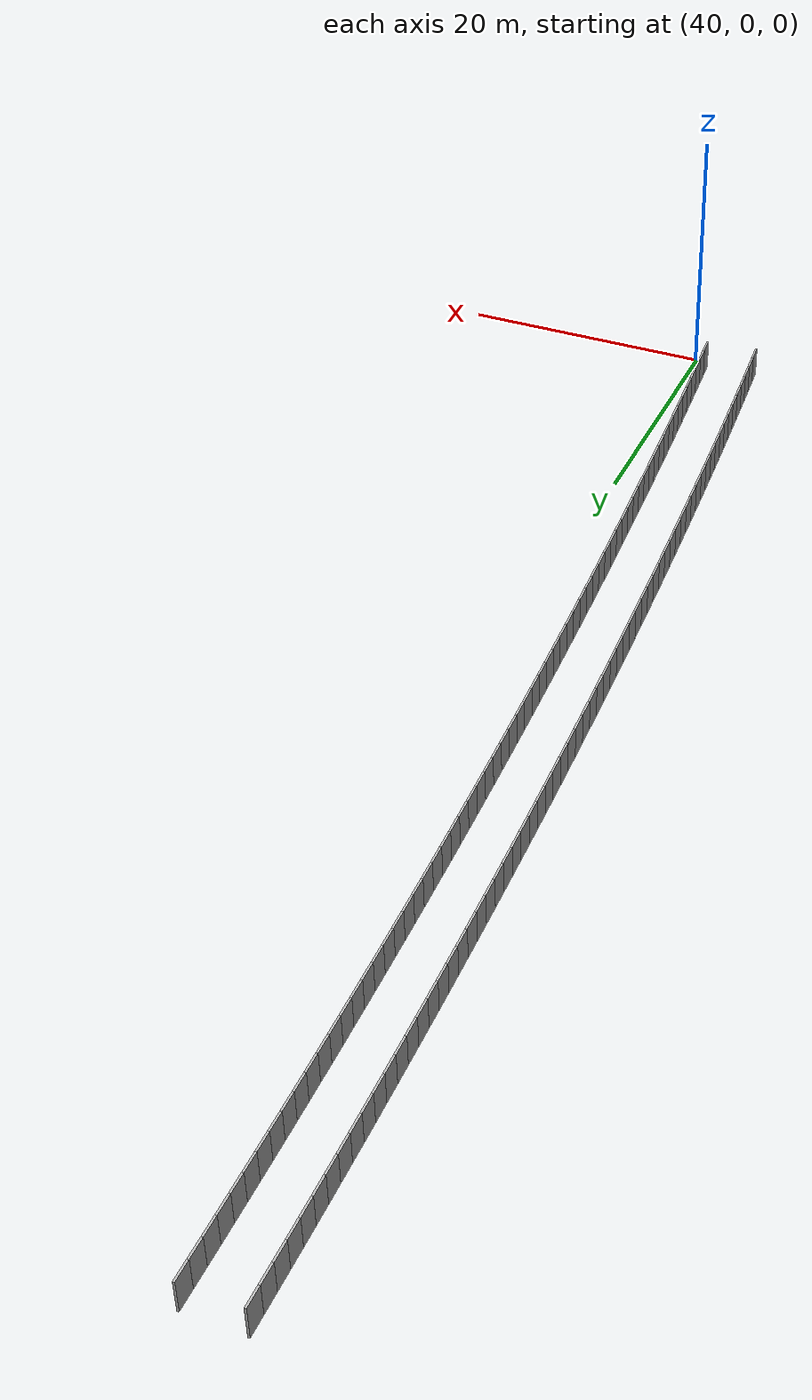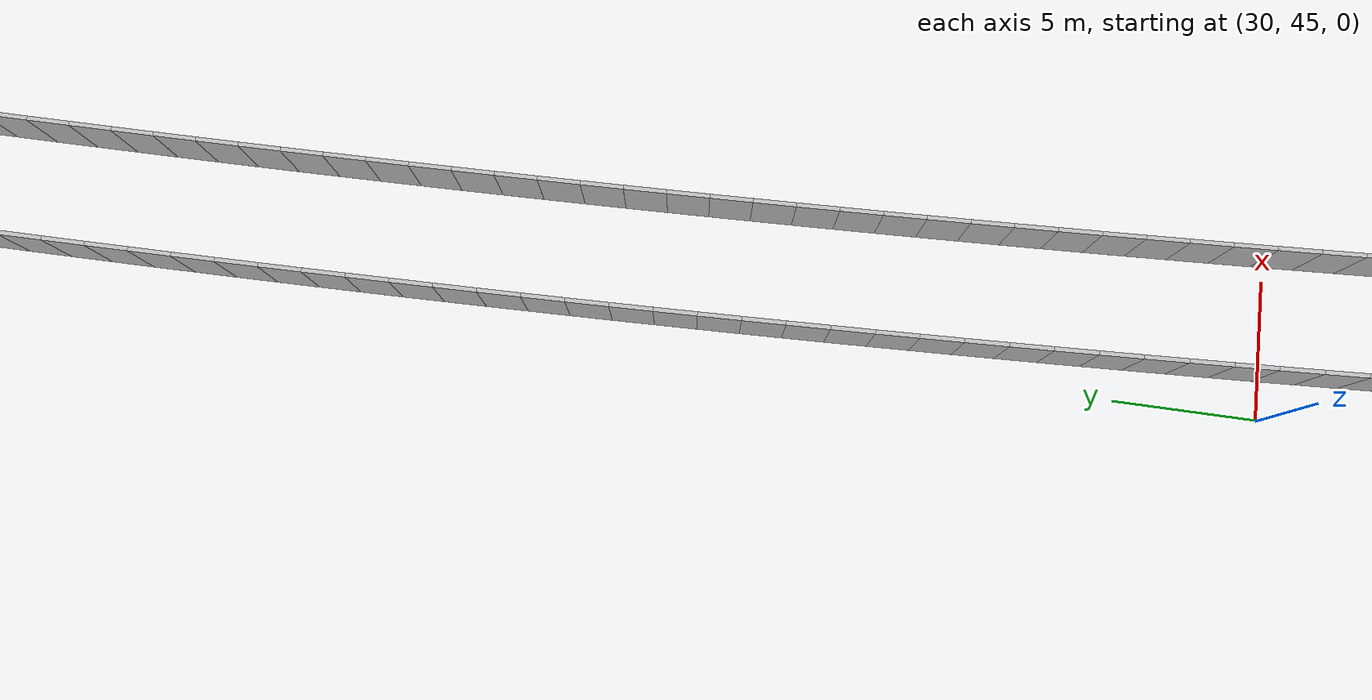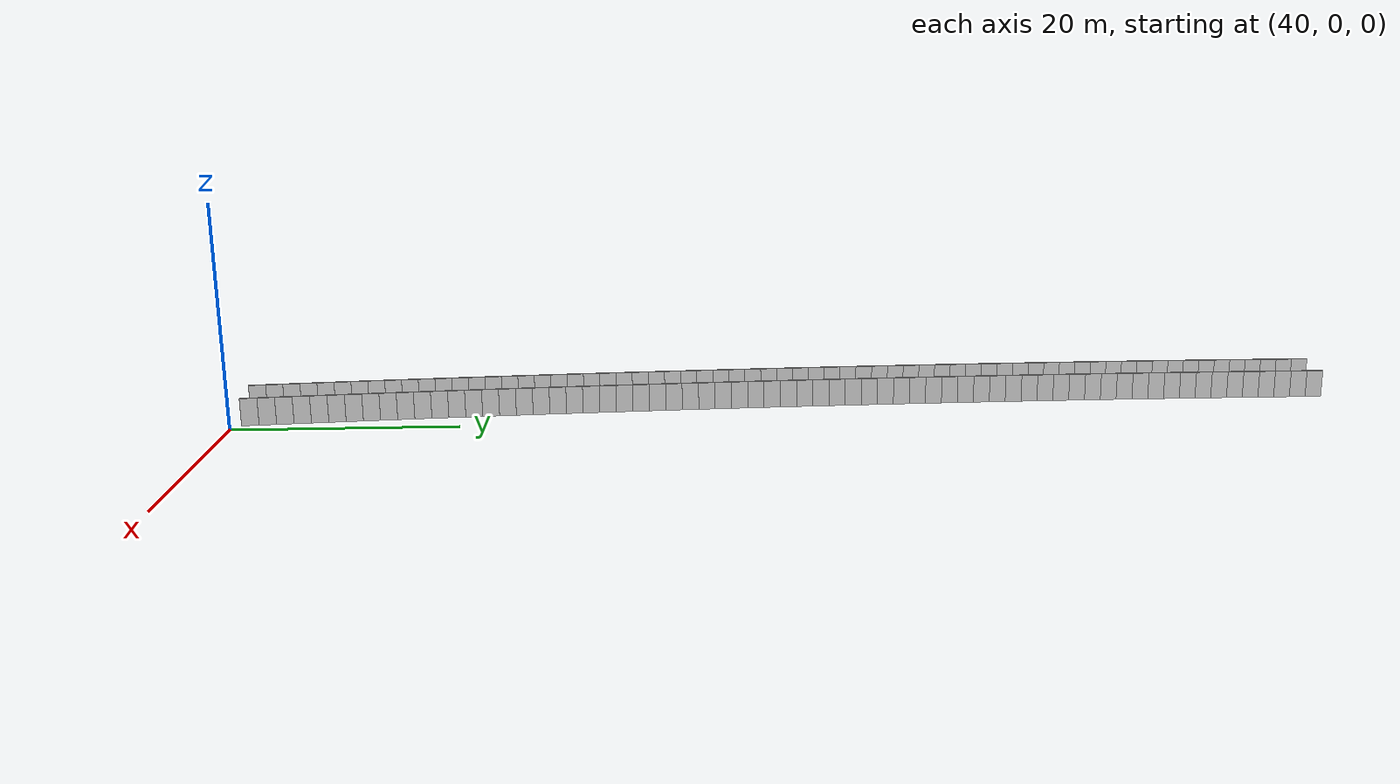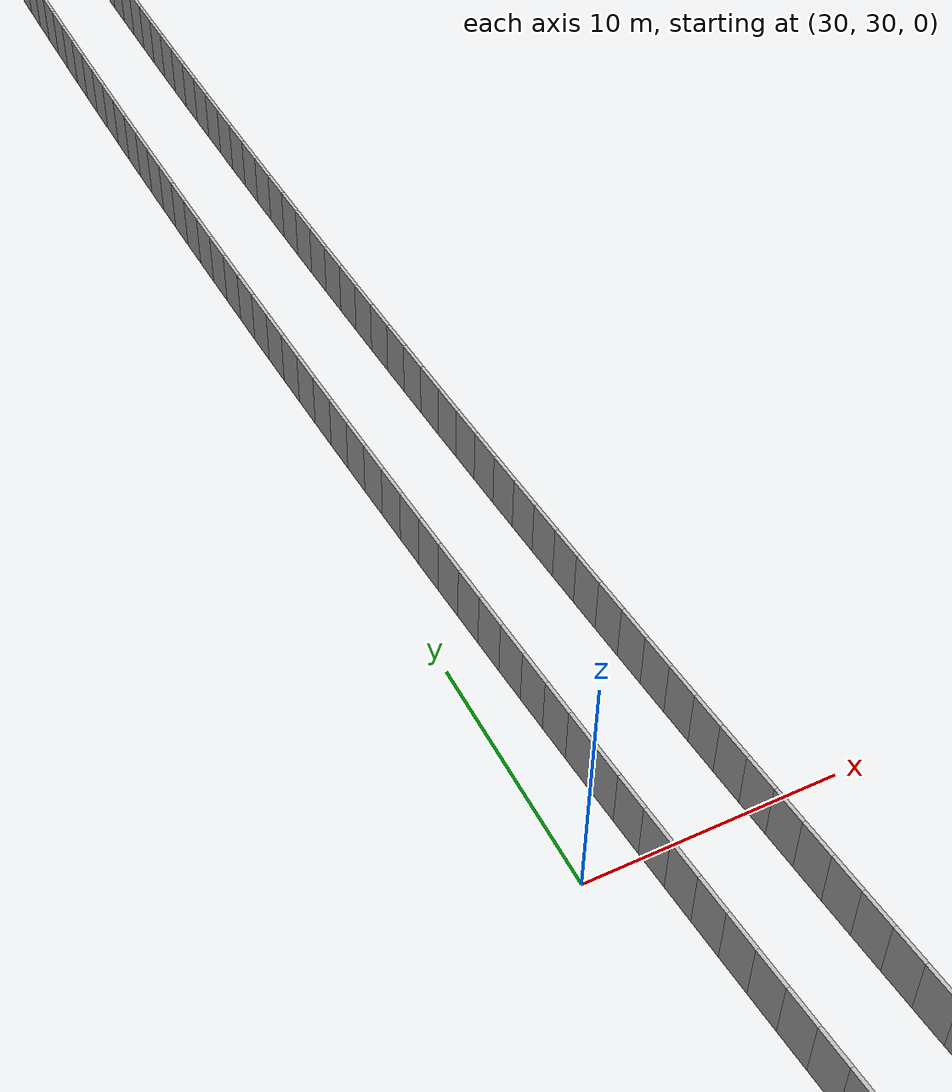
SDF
<?xml version="1.0" ?>
<sdf version="1.6">
  <model name="sps_0112">
    <pose frame="">0 0 0 0 -0 0</pose>
    <static>1</static>
    <self_collide>0</self_collide>
    <allow_auto_disable>0</allow_auto_disable>
    <link name="Wall5244">
      <kinematic>0</kinematic>
      <gravity>1</gravity>
      <self_collide>0</self_collide>
      <collision name="collision">
        <geometry>
          <box>
            <size>1.49643 0.15 2.5</size>
          </box>
        </geometry>
        <pose frame="">0 0 0 0 -0 0</pose>
      </collision>
      <visual name="visual">
        <geometry>
          <box>
            <size>1.49643 0.15 2.5</size>
          </box>
        </geometry>
        <pose frame="">0 0 0 0 -0 0</pose>
        <cast_shadows>1</cast_shadows>
        <transparency>0.0</transparency>
      </visual>
      <pose frame="">34.4289 98.5549 1.25 0 0 -1.57691</pose>
    </link>
    <link name="Wall5245">
      <kinematic>0</kinematic>
      <gravity>1</gravity>
      <self_collide>0</self_collide>
      <collision name="collision">
        <geometry>
          <box>
            <size>1.49666 0.15 2.5</size>
          </box>
        </geometry>
        <pose frame="">0 0 0 0 -0 0</pose>
      </collision>
      <visual name="visual">
        <geometry>
          <box>
            <size>1.49666 0.15 2.5</size>
          </box>
        </geometry>
        <pose frame="">0 0 0 0 -0 0</pose>
        <cast_shadows>1</cast_shadows>
        <transparency>0.0</transparency>
      </visual>
      <pose frame="">34.4209 97.0584 1.25 0 0 -1.57536</pose>
    </link>
    <link name="Wall5246">
      <kinematic>0</kinematic>
      <gravity>1</gravity>
      <self_collide>0</self_collide>
      <collision name="collision">
        <geometry>
          <box>
            <size>1.49641 0.15 2.5</size>
          </box>
        </geometry>
        <pose frame="">0 0 0 0 -0 0</pose>
      </collision>
      <visual name="visual">
        <geometry>
          <box>
            <size>1.49641 0.15 2.5</size>
          </box>
        </geometry>
        <pose frame="">0 0 0 0 -0 0</pose>
        <cast_shadows>1</cast_shadows>
        <transparency>0.0</transparency>
      </visual>
      <pose frame="">34.4152 95.5619 1.25 0 0 -1.57386</pose>
    </link>
    <link name="Wall5247">
      <kinematic>0</kinematic>
      <gravity>1</gravity>
      <self_collide>0</self_collide>
      <collision name="collision">
        <geometry>
          <box>
            <size>1.49658 0.15 2.5</size>
          </box>
        </geometry>
        <pose frame="">0 0 0 0 -0 0</pose>
      </collision>
      <visual name="visual">
        <geometry>
          <box>
            <size>1.49658 0.15 2.5</size>
          </box>
        </geometry>
        <pose frame="">0 0 0 0 -0 0</pose>
        <cast_shadows>1</cast_shadows>
        <transparency>0.0</transparency>
      </visual>
      <pose frame="">34.4118 94.0654 1.25 0 0 -1.57226</pose>
    </link>
    <link name="Wall5248">
      <kinematic>0</kinematic>
      <gravity>1</gravity>
      <self_collide>0</self_collide>
      <collision name="collision">
        <geometry>
          <box>
            <size>1.49658 0.15 2.5</size>
          </box>
        </geometry>
        <pose frame="">0 0 0 0 -0 0</pose>
      </collision>
      <visual name="visual">
        <geometry>
          <box>
            <size>1.49658 0.15 2.5</size>
          </box>
        </geometry>
        <pose frame="">0 0 0 0 -0 0</pose>
        <cast_shadows>1</cast_shadows>
        <transparency>0.0</transparency>
      </visual>
      <pose frame="">34.4108 92.5688 1.25 0 0 -1.57067</pose>
    </link>
    <link name="Wall5249">
      <kinematic>0</kinematic>
      <gravity>1</gravity>
      <self_collide>0</self_collide>
      <collision name="collision">
        <geometry>
          <box>
            <size>1.4964 0.15 2.5</size>
          </box>
        </geometry>
        <pose frame="">0 0 0 0 -0 0</pose>
      </collision>
      <visual name="visual">
        <geometry>
          <box>
            <size>1.4964 0.15 2.5</size>
          </box>
        </geometry>
        <pose frame="">0 0 0 0 -0 0</pose>
        <cast_shadows>1</cast_shadows>
        <transparency>0.0</transparency>
      </visual>
      <pose frame="">34.4122 91.0723 1.25 0 0 -1.56904</pose>
    </link>
    <link name="Wall5250">
      <kinematic>0</kinematic>
      <gravity>1</gravity>
      <self_collide>0</self_collide>
      <collision name="collision">
        <geometry>
          <box>
            <size>1.49665 0.15 2.5</size>
          </box>
        </geometry>
        <pose frame="">0 0 0 0 -0 0</pose>
      </collision>
      <visual name="visual">
        <geometry>
          <box>
            <size>1.49665 0.15 2.5</size>
          </box>
        </geometry>
        <pose frame="">0 0 0 0 -0 0</pose>
        <cast_shadows>1</cast_shadows>
        <transparency>0.0</transparency>
      </visual>
      <pose frame="">34.416 89.5758 1.25 0 0 -1.56745</pose>
    </link>
    <link name="Wall5251">
      <kinematic>0</kinematic>
      <gravity>1</gravity>
      <self_collide>0</self_collide>
      <collision name="collision">
        <geometry>
          <box>
            <size>1.49642 0.15 2.5</size>
          </box>
        </geometry>
        <pose frame="">0 0 0 0 -0 0</pose>
      </collision>
      <visual name="visual">
        <geometry>
          <box>
            <size>1.49642 0.15 2.5</size>
          </box>
        </geometry>
        <pose frame="">0 0 0 0 -0 0</pose>
        <cast_shadows>1</cast_shadows>
        <transparency>0.0</transparency>
      </visual>
      <pose frame="">34.4222 88.0793 1.25 0 0 -1.56586</pose>
    </link>
    <link name="Wall5252">
      <kinematic>0</kinematic>
      <gravity>1</gravity>
      <self_collide>0</self_collide>
      <collision name="collision">
        <geometry>
          <box>
            <size>1.49661 0.15 2.5</size>
          </box>
        </geometry>
        <pose frame="">0 0 0 0 -0 0</pose>
      </collision>
      <visual name="visual">
        <geometry>
          <box>
            <size>1.49661 0.15 2.5</size>
          </box>
        </geometry>
        <pose frame="">0 0 0 0 -0 0</pose>
        <cast_shadows>1</cast_shadows>
        <transparency>0.0</transparency>
      </visual>
      <pose frame="">34.4307 86.5828 1.25 0 0 -1.56427</pose>
    </link>
    <link name="Wall5253">
      <kinematic>0</kinematic>
      <gravity>1</gravity>
      <self_collide>0</self_collide>
      <collision name="collision">
        <geometry>
          <box>
            <size>1.49645 0.15 2.5</size>
          </box>
        </geometry>
        <pose frame="">0 0 0 0 -0 0</pose>
      </collision>
      <visual name="visual">
        <geometry>
          <box>
            <size>1.49645 0.15 2.5</size>
          </box>
        </geometry>
        <pose frame="">0 0 0 0 -0 0</pose>
        <cast_shadows>1</cast_shadows>
        <transparency>0.0</transparency>
      </visual>
      <pose frame="">34.4416 85.0863 1.25 0 0 -1.56276</pose>
    </link>
    <link name="Wall5254">
      <kinematic>0</kinematic>
      <gravity>1</gravity>
      <self_collide>0</self_collide>
      <collision name="collision">
        <geometry>
          <box>
            <size>1.49665 0.15 2.5</size>
          </box>
        </geometry>
        <pose frame="">0 0 0 0 -0 0</pose>
      </collision>
      <visual name="visual">
        <geometry>
          <box>
            <size>1.49665 0.15 2.5</size>
          </box>
        </geometry>
        <pose frame="">0 0 0 0 -0 0</pose>
        <cast_shadows>1</cast_shadows>
        <transparency>0.0</transparency>
      </visual>
      <pose frame="">34.4549 83.5898 1.25 0 0 -1.56117</pose>
    </link>
    <link name="Wall5255">
      <kinematic>0</kinematic>
      <gravity>1</gravity>
      <self_collide>0</self_collide>
      <collision name="collision">
        <geometry>
          <box>
            <size>1.4965 0.15 2.5</size>
          </box>
        </geometry>
        <pose frame="">0 0 0 0 -0 0</pose>
      </collision>
      <visual name="visual">
        <geometry>
          <box>
            <size>1.4965 0.15 2.5</size>
          </box>
        </geometry>
        <pose frame="">0 0 0 0 -0 0</pose>
        <cast_shadows>1</cast_shadows>
        <transparency>0.0</transparency>
      </visual>
      <pose frame="">34.4705 82.0933 1.25 0 0 -1.55946</pose>
    </link>
    <link name="Wall5256">
      <kinematic>0</kinematic>
      <gravity>1</gravity>
      <self_collide>0</self_collide>
      <collision name="collision">
        <geometry>
          <box>
            <size>1.49652 0.15 2.5</size>
          </box>
        </geometry>
        <pose frame="">0 0 0 0 -0 0</pose>
      </collision>
      <visual name="visual">
        <geometry>
          <box>
            <size>1.49652 0.15 2.5</size>
          </box>
        </geometry>
        <pose frame="">0 0 0 0 -0 0</pose>
        <cast_shadows>1</cast_shadows>
        <transparency>0.0</transparency>
      </visual>
      <pose frame="">34.4886 80.5969 1.25 0 0 -1.55795</pose>
    </link>
    <link name="Wall5257">
      <kinematic>0</kinematic>
      <gravity>1</gravity>
      <self_collide>0</self_collide>
      <collision name="collision">
        <geometry>
          <box>
            <size>1.49637 0.15 2.5</size>
          </box>
        </geometry>
        <pose frame="">0 0 0 0 -0 0</pose>
      </collision>
      <visual name="visual">
        <geometry>
          <box>
            <size>1.49637 0.15 2.5</size>
          </box>
        </geometry>
        <pose frame="">0 0 0 0 -0 0</pose>
        <cast_shadows>1</cast_shadows>
        <transparency>0.0</transparency>
      </visual>
      <pose frame="">34.5091 79.1006 1.25 0 0 -1.55636</pose>
    </link>
    <link name="Wall5258">
      <kinematic>0</kinematic>
      <gravity>1</gravity>
      <self_collide>0</self_collide>
      <collision name="collision">
        <geometry>
          <box>
            <size>1.49659 0.15 2.5</size>
          </box>
        </geometry>
        <pose frame="">0 0 0 0 -0 0</pose>
      </collision>
      <visual name="visual">
        <geometry>
          <box>
            <size>1.49659 0.15 2.5</size>
          </box>
        </geometry>
        <pose frame="">0 0 0 0 -0 0</pose>
        <cast_shadows>1</cast_shadows>
        <transparency>0.0</transparency>
      </visual>
      <pose frame="">34.5319 77.6043 1.25 0 0 -1.55477</pose>
    </link>
    <link name="Wall5259">
      <kinematic>0</kinematic>
      <gravity>1</gravity>
      <self_collide>0</self_collide>
      <collision name="collision">
        <geometry>
          <box>
            <size>1.49644 0.15 2.5</size>
          </box>
        </geometry>
        <pose frame="">0 0 0 0 -0 0</pose>
      </collision>
      <visual name="visual">
        <geometry>
          <box>
            <size>1.49644 0.15 2.5</size>
          </box>
        </geometry>
        <pose frame="">0 0 0 0 -0 0</pose>
        <cast_shadows>1</cast_shadows>
        <transparency>0.0</transparency>
      </visual>
      <pose frame="">34.5569 76.108 1.25 0 0 -1.5533</pose>
    </link>
    <link name="Wall5260">
      <kinematic>0</kinematic>
      <gravity>1</gravity>
      <self_collide>0</self_collide>
      <collision name="collision">
        <geometry>
          <box>
            <size>1.49668 0.15 2.5</size>
          </box>
        </geometry>
        <pose frame="">0 0 0 0 -0 0</pose>
      </collision>
      <visual name="visual">
        <geometry>
          <box>
            <size>1.49668 0.15 2.5</size>
          </box>
        </geometry>
        <pose frame="">0 0 0 0 -0 0</pose>
        <cast_shadows>1</cast_shadows>
        <transparency>0.0</transparency>
      </visual>
      <pose frame="">34.5844 74.6117 1.25 0 0 -1.55155</pose>
    </link>
    <link name="Wall5261">
      <kinematic>0</kinematic>
      <gravity>1</gravity>
      <self_collide>0</self_collide>
      <collision name="collision">
        <geometry>
          <box>
            <size>1.49654 0.15 2.5</size>
          </box>
        </geometry>
        <pose frame="">0 0 0 0 -0 0</pose>
      </collision>
      <visual name="visual">
        <geometry>
          <box>
            <size>1.49654 0.15 2.5</size>
          </box>
        </geometry>
        <pose frame="">0 0 0 0 -0 0</pose>
        <cast_shadows>1</cast_shadows>
        <transparency>0.0</transparency>
      </visual>
      <pose frame="">34.6143 73.1154 1.25 0 0 -1.55008</pose>
    </link>
    <link name="Wall5262">
      <kinematic>0</kinematic>
      <gravity>1</gravity>
      <self_collide>0</self_collide>
      <collision name="collision">
        <geometry>
          <box>
            <size>1.49634 0.15 2.5</size>
          </box>
        </geometry>
        <pose frame="">0 0 0 0 -0 0</pose>
      </collision>
      <visual name="visual">
        <geometry>
          <box>
            <size>1.49634 0.15 2.5</size>
          </box>
        </geometry>
        <pose frame="">0 0 0 0 -0 0</pose>
        <cast_shadows>1</cast_shadows>
        <transparency>0.0</transparency>
      </visual>
      <pose frame="">34.6465 71.6193 1.25 0 0 -1.54848</pose>
    </link>
    <link name="Wall5263">
      <kinematic>0</kinematic>
      <gravity>1</gravity>
      <self_collide>0</self_collide>
      <collision name="collision">
        <geometry>
          <box>
            <size>1.49664 0.15 2.5</size>
          </box>
        </geometry>
        <pose frame="">0 0 0 0 -0 0</pose>
      </collision>
      <visual name="visual">
        <geometry>
          <box>
            <size>1.49664 0.15 2.5</size>
          </box>
        </geometry>
        <pose frame="">0 0 0 0 -0 0</pose>
        <cast_shadows>1</cast_shadows>
        <transparency>0.0</transparency>
      </visual>
      <pose frame="">34.6811 70.1232 1.25 0 0 -1.54686</pose>
    </link>
    <link name="Wall5264">
      <kinematic>0</kinematic>
      <gravity>1</gravity>
      <self_collide>0</self_collide>
      <collision name="collision">
        <geometry>
          <box>
            <size>1.49646 0.15 2.5</size>
          </box>
        </geometry>
        <pose frame="">0 0 0 0 -0 0</pose>
      </collision>
      <visual name="visual">
        <geometry>
          <box>
            <size>1.49646 0.15 2.5</size>
          </box>
        </geometry>
        <pose frame="">0 0 0 0 -0 0</pose>
        <cast_shadows>1</cast_shadows>
        <transparency>0.0</transparency>
      </visual>
      <pose frame="">34.7182 68.6271 1.25 0 0 -1.54526</pose>
    </link>
    <link name="Wall5265">
      <kinematic>0</kinematic>
      <gravity>1</gravity>
      <self_collide>0</self_collide>
      <collision name="collision">
        <geometry>
          <box>
            <size>1.49658 0.15 2.5</size>
          </box>
        </geometry>
        <pose frame="">0 0 0 0 -0 0</pose>
      </collision>
      <visual name="visual">
        <geometry>
          <box>
            <size>1.49658 0.15 2.5</size>
          </box>
        </geometry>
        <pose frame="">0 0 0 0 -0 0</pose>
        <cast_shadows>1</cast_shadows>
        <transparency>0.0</transparency>
      </visual>
      <pose frame="">34.7576 67.1311 1.25 0 0 -1.54367</pose>
    </link>
    <link name="Wall5266">
      <kinematic>0</kinematic>
      <gravity>1</gravity>
      <self_collide>0</self_collide>
      <collision name="collision">
        <geometry>
          <box>
            <size>1.49659 0.15 2.5</size>
          </box>
        </geometry>
        <pose frame="">0 0 0 0 -0 0</pose>
      </collision>
      <visual name="visual">
        <geometry>
          <box>
            <size>1.49659 0.15 2.5</size>
          </box>
        </geometry>
        <pose frame="">0 0 0 0 -0 0</pose>
        <cast_shadows>1</cast_shadows>
        <transparency>0.0</transparency>
      </visual>
      <pose frame="">34.7994 65.6351 1.25 0 0 -1.54204</pose>
    </link>
    <link name="Wall5267">
      <kinematic>0</kinematic>
      <gravity>1</gravity>
      <self_collide>0</self_collide>
      <collision name="collision">
        <geometry>
          <box>
            <size>1.49647 0.15 2.5</size>
          </box>
        </geometry>
        <pose frame="">0 0 0 0 -0 0</pose>
      </collision>
      <visual name="visual">
        <geometry>
          <box>
            <size>1.49647 0.15 2.5</size>
          </box>
        </geometry>
        <pose frame="">0 0 0 0 -0 0</pose>
        <cast_shadows>1</cast_shadows>
        <transparency>0.0</transparency>
      </visual>
      <pose frame="">34.8435 64.1392 1.25 0 0 -1.54061</pose>
    </link>
    <link name="Wall5268">
      <kinematic>0</kinematic>
      <gravity>1</gravity>
      <self_collide>0</self_collide>
      <collision name="collision">
        <geometry>
          <box>
            <size>1.49655 0.15 2.5</size>
          </box>
        </geometry>
        <pose frame="">0 0 0 0 -0 0</pose>
      </collision>
      <visual name="visual">
        <geometry>
          <box>
            <size>1.49655 0.15 2.5</size>
          </box>
        </geometry>
        <pose frame="">0 0 0 0 -0 0</pose>
        <cast_shadows>1</cast_shadows>
        <transparency>0.0</transparency>
      </visual>
      <pose frame="">34.8899 62.6434 1.25 0 0 -1.53886</pose>
    </link>
    <link name="Wall5269">
      <kinematic>0</kinematic>
      <gravity>1</gravity>
      <self_collide>0</self_collide>
      <collision name="collision">
        <geometry>
          <box>
            <size>1.49644 0.15 2.5</size>
          </box>
        </geometry>
        <pose frame="">0 0 0 0 -0 0</pose>
      </collision>
      <visual name="visual">
        <geometry>
          <box>
            <size>1.49644 0.15 2.5</size>
          </box>
        </geometry>
        <pose frame="">0 0 0 0 -0 0</pose>
        <cast_shadows>1</cast_shadows>
        <transparency>0.0</transparency>
      </visual>
      <pose frame="">34.9388 61.1477 1.25 0 0 -1.53739</pose>
    </link>
    <link name="Wall5270">
      <kinematic>0</kinematic>
      <gravity>1</gravity>
      <self_collide>0</self_collide>
      <collision name="collision">
        <geometry>
          <box>
            <size>1.49652 0.15 2.5</size>
          </box>
        </geometry>
        <pose frame="">0 0 0 0 -0 0</pose>
      </collision>
      <visual name="visual">
        <geometry>
          <box>
            <size>1.49652 0.15 2.5</size>
          </box>
        </geometry>
        <pose frame="">0 0 0 0 -0 0</pose>
        <cast_shadows>1</cast_shadows>
        <transparency>0.0</transparency>
      </visual>
      <pose frame="">34.99 59.6521 1.25 0 0 -1.53576</pose>
    </link>
    <link name="Wall5271">
      <kinematic>0</kinematic>
      <gravity>1</gravity>
      <self_collide>0</self_collide>
      <collision name="collision">
        <geometry>
          <box>
            <size>1.49661 0.15 2.5</size>
          </box>
        </geometry>
        <pose frame="">0 0 0 0 -0 0</pose>
      </collision>
      <visual name="visual">
        <geometry>
          <box>
            <size>1.49661 0.15 2.5</size>
          </box>
        </geometry>
        <pose frame="">0 0 0 0 -0 0</pose>
        <cast_shadows>1</cast_shadows>
        <transparency>0.0</transparency>
      </visual>
      <pose frame="">35.0437 58.1565 1.25 0 0 -1.53417</pose>
    </link>
    <link name="Wall5272">
      <kinematic>0</kinematic>
      <gravity>1</gravity>
      <self_collide>0</self_collide>
      <collision name="collision">
        <geometry>
          <box>
            <size>1.4967 0.15 2.5</size>
          </box>
        </geometry>
        <pose frame="">0 0 0 0 -0 0</pose>
      </collision>
      <visual name="visual">
        <geometry>
          <box>
            <size>1.4967 0.15 2.5</size>
          </box>
        </geometry>
        <pose frame="">0 0 0 0 -0 0</pose>
        <cast_shadows>1</cast_shadows>
        <transparency>0.0</transparency>
      </visual>
      <pose frame="">35.0997 56.6609 1.25 0 0 -1.53258</pose>
    </link>
    <link name="Wall5273">
      <kinematic>0</kinematic>
      <gravity>1</gravity>
      <self_collide>0</self_collide>
      <collision name="collision">
        <geometry>
          <box>
            <size>1.49636 0.15 2.5</size>
          </box>
        </geometry>
        <pose frame="">0 0 0 0 -0 0</pose>
      </collision>
      <visual name="visual">
        <geometry>
          <box>
            <size>1.49636 0.15 2.5</size>
          </box>
        </geometry>
        <pose frame="">0 0 0 0 -0 0</pose>
        <cast_shadows>1</cast_shadows>
        <transparency>0.0</transparency>
      </visual>
      <pose frame="">35.158 55.1655 1.25 0 0 -1.5311</pose>
    </link>
    <link name="Wall5274">
      <kinematic>0</kinematic>
      <gravity>1</gravity>
      <self_collide>0</self_collide>
      <collision name="collision">
        <geometry>
          <box>
            <size>1.49652 0.15 2.5</size>
          </box>
        </geometry>
        <pose frame="">0 0 0 0 -0 0</pose>
      </collision>
      <visual name="visual">
        <geometry>
          <box>
            <size>1.49652 0.15 2.5</size>
          </box>
        </geometry>
        <pose frame="">0 0 0 0 -0 0</pose>
        <cast_shadows>1</cast_shadows>
        <transparency>0.0</transparency>
      </visual>
      <pose frame="">35.2186 53.6703 1.25 0 0 -1.52947</pose>
    </link>
    <link name="Wall5275">
      <kinematic>0</kinematic>
      <gravity>1</gravity>
      <self_collide>0</self_collide>
      <collision name="collision">
        <geometry>
          <box>
            <size>1.49656 0.15 2.5</size>
          </box>
        </geometry>
        <pose frame="">0 0 0 0 -0 0</pose>
      </collision>
      <visual name="visual">
        <geometry>
          <box>
            <size>1.49656 0.15 2.5</size>
          </box>
        </geometry>
        <pose frame="">0 0 0 0 -0 0</pose>
        <cast_shadows>1</cast_shadows>
        <transparency>0.0</transparency>
      </visual>
      <pose frame="">35.2816 52.1751 1.25 0 0 -1.52788</pose>
    </link>
    <link name="Wall5276">
      <kinematic>0</kinematic>
      <gravity>1</gravity>
      <self_collide>0</self_collide>
      <collision name="collision">
        <geometry>
          <box>
            <size>1.49649 0.15 2.5</size>
          </box>
        </geometry>
        <pose frame="">0 0 0 0 -0 0</pose>
      </collision>
      <visual name="visual">
        <geometry>
          <box>
            <size>1.49649 0.15 2.5</size>
          </box>
        </geometry>
        <pose frame="">0 0 0 0 -0 0</pose>
        <cast_shadows>1</cast_shadows>
        <transparency>0.0</transparency>
      </visual>
      <pose frame="">35.3471 50.68 1.25 0 0 -1.52616</pose>
    </link>
    <link name="Wall5277">
      <kinematic>0</kinematic>
      <gravity>1</gravity>
      <self_collide>0</self_collide>
      <collision name="collision">
        <geometry>
          <box>
            <size>1.49659 0.15 2.5</size>
          </box>
        </geometry>
        <pose frame="">0 0 0 0 -0 0</pose>
      </collision>
      <visual name="visual">
        <geometry>
          <box>
            <size>1.49659 0.15 2.5</size>
          </box>
        </geometry>
        <pose frame="">0 0 0 0 -0 0</pose>
        <cast_shadows>1</cast_shadows>
        <transparency>0.0</transparency>
      </visual>
      <pose frame="">35.415 49.185 1.25 0 0 -1.52465</pose>
    </link>
    <link name="Wall5278">
      <kinematic>0</kinematic>
      <gravity>1</gravity>
      <self_collide>0</self_collide>
      <collision name="collision">
        <geometry>
          <box>
            <size>1.49651 0.15 2.5</size>
          </box>
        </geometry>
        <pose frame="">0 0 0 0 -0 0</pose>
      </collision>
      <visual name="visual">
        <geometry>
          <box>
            <size>1.49651 0.15 2.5</size>
          </box>
        </geometry>
        <pose frame="">0 0 0 0 -0 0</pose>
        <cast_shadows>1</cast_shadows>
        <transparency>0.0</transparency>
      </visual>
      <pose frame="">35.4852 47.6901 1.25 0 0 -1.5231</pose>
    </link>
    <link name="Wall5279">
      <kinematic>0</kinematic>
      <gravity>1</gravity>
      <self_collide>0</self_collide>
      <collision name="collision">
        <geometry>
          <box>
            <size>1.49644 0.15 2.5</size>
          </box>
        </geometry>
        <pose frame="">0 0 0 0 -0 0</pose>
      </collision>
      <visual name="visual">
        <geometry>
          <box>
            <size>1.49644 0.15 2.5</size>
          </box>
        </geometry>
        <pose frame="">0 0 0 0 -0 0</pose>
        <cast_shadows>1</cast_shadows>
        <transparency>0.0</transparency>
      </visual>
      <pose frame="">35.5576 46.1954 1.25 0 0 -1.52159</pose>
    </link>
    <link name="Wall5280">
      <kinematic>0</kinematic>
      <gravity>1</gravity>
      <self_collide>0</self_collide>
      <collision name="collision">
        <geometry>
          <box>
            <size>1.49669 0.15 2.5</size>
          </box>
        </geometry>
        <pose frame="">0 0 0 0 -0 0</pose>
      </collision>
      <visual name="visual">
        <geometry>
          <box>
            <size>1.49669 0.15 2.5</size>
          </box>
        </geometry>
        <pose frame="">0 0 0 0 -0 0</pose>
        <cast_shadows>1</cast_shadows>
        <transparency>0.0</transparency>
      </visual>
      <pose frame="">35.6326 44.7007 1.25 0 0 -1.51984</pose>
    </link>
    <link name="Wall5281">
      <kinematic>0</kinematic>
      <gravity>1</gravity>
      <self_collide>0</self_collide>
      <collision name="collision">
        <geometry>
          <box>
            <size>1.4965 0.15 2.5</size>
          </box>
        </geometry>
        <pose frame="">0 0 0 0 -0 0</pose>
      </collision>
      <visual name="visual">
        <geometry>
          <box>
            <size>1.4965 0.15 2.5</size>
          </box>
        </geometry>
        <pose frame="">0 0 0 0 -0 0</pose>
        <cast_shadows>1</cast_shadows>
        <transparency>0.0</transparency>
      </visual>
      <pose frame="">35.7099 43.2061 1.25 0 0 -1.5184</pose>
    </link>
    <link name="Wall5282">
      <kinematic>0</kinematic>
      <gravity>1</gravity>
      <self_collide>0</self_collide>
      <collision name="collision">
        <geometry>
          <box>
            <size>1.49657 0.15 2.5</size>
          </box>
        </geometry>
        <pose frame="">0 0 0 0 -0 0</pose>
      </collision>
      <visual name="visual">
        <geometry>
          <box>
            <size>1.49657 0.15 2.5</size>
          </box>
        </geometry>
        <pose frame="">0 0 0 0 -0 0</pose>
        <cast_shadows>1</cast_shadows>
        <transparency>0.0</transparency>
      </visual>
      <pose frame="">35.7895 41.7117 1.25 0 0 -1.51677</pose>
    </link>
    <link name="Wall5283">
      <kinematic>0</kinematic>
      <gravity>1</gravity>
      <self_collide>0</self_collide>
      <collision name="collision">
        <geometry>
          <box>
            <size>1.49633 0.15 2.5</size>
          </box>
        </geometry>
        <pose frame="">0 0 0 0 -0 0</pose>
      </collision>
      <visual name="visual">
        <geometry>
          <box>
            <size>1.49633 0.15 2.5</size>
          </box>
        </geometry>
        <pose frame="">0 0 0 0 -0 0</pose>
        <cast_shadows>1</cast_shadows>
        <transparency>0.0</transparency>
      </visual>
      <pose frame="">35.8715 40.2175 1.25 0 0 -1.51517</pose>
    </link>
    <link name="Wall5284">
      <kinematic>0</kinematic>
      <gravity>1</gravity>
      <self_collide>0</self_collide>
      <collision name="collision">
        <geometry>
          <box>
            <size>1.49664 0.15 2.5</size>
          </box>
        </geometry>
        <pose frame="">0 0 0 0 -0 0</pose>
      </collision>
      <visual name="visual">
        <geometry>
          <box>
            <size>1.49664 0.15 2.5</size>
          </box>
        </geometry>
        <pose frame="">0 0 0 0 -0 0</pose>
        <cast_shadows>1</cast_shadows>
        <transparency>0.0</transparency>
      </visual>
      <pose frame="">35.9557 38.7234 1.25 0 0 -1.51371</pose>
    </link>
    <link name="Wall5285">
      <kinematic>0</kinematic>
      <gravity>1</gravity>
      <self_collide>0</self_collide>
      <collision name="collision">
        <geometry>
          <box>
            <size>1.49655 0.15 2.5</size>
          </box>
        </geometry>
        <pose frame="">0 0 0 0 -0 0</pose>
      </collision>
      <visual name="visual">
        <geometry>
          <box>
            <size>1.49655 0.15 2.5</size>
          </box>
        </geometry>
        <pose frame="">0 0 0 0 -0 0</pose>
        <cast_shadows>1</cast_shadows>
        <transparency>0.0</transparency>
      </visual>
      <pose frame="">36.0424 37.2293 1.25 0 0 -1.51195</pose>
    </link>
    <link name="Wall5286">
      <kinematic>0</kinematic>
      <gravity>1</gravity>
      <self_collide>0</self_collide>
      <collision name="collision">
        <geometry>
          <box>
            <size>1.49656 0.15 2.5</size>
          </box>
        </geometry>
        <pose frame="">0 0 0 0 -0 0</pose>
      </collision>
      <visual name="visual">
        <geometry>
          <box>
            <size>1.49656 0.15 2.5</size>
          </box>
        </geometry>
        <pose frame="">0 0 0 0 -0 0</pose>
        <cast_shadows>1</cast_shadows>
        <transparency>0.0</transparency>
      </visual>
      <pose frame="">36.1316 35.7354 1.25 0 0 -1.51048</pose>
    </link>
    <link name="Wall5287">
      <kinematic>0</kinematic>
      <gravity>1</gravity>
      <self_collide>0</self_collide>
      <collision name="collision">
        <geometry>
          <box>
            <size>1.49647 0.15 2.5</size>
          </box>
        </geometry>
        <pose frame="">0 0 0 0 -0 0</pose>
      </collision>
      <visual name="visual">
        <geometry>
          <box>
            <size>1.49647 0.15 2.5</size>
          </box>
        </geometry>
        <pose frame="">0 0 0 0 -0 0</pose>
        <cast_shadows>1</cast_shadows>
        <transparency>0.0</transparency>
      </visual>
      <pose frame="">36.223 34.2417 1.25 0 0 -1.50876</pose>
    </link>
    <link name="Wall5288">
      <kinematic>0</kinematic>
      <gravity>1</gravity>
      <self_collide>0</self_collide>
      <collision name="collision">
        <geometry>
          <box>
            <size>1.49643 0.15 2.5</size>
          </box>
        </geometry>
        <pose frame="">0 0 0 0 -0 0</pose>
      </collision>
      <visual name="visual">
        <geometry>
          <box>
            <size>1.49643 0.15 2.5</size>
          </box>
        </geometry>
        <pose frame="">0 0 0 0 -0 0</pose>
        <cast_shadows>1</cast_shadows>
        <transparency>0.0</transparency>
      </visual>
      <pose frame="">36.3169 32.7482 1.25 0 0 -1.50725</pose>
    </link>
    <link name="Wall5289">
      <kinematic>0</kinematic>
      <gravity>1</gravity>
      <self_collide>0</self_collide>
      <collision name="collision">
        <geometry>
          <box>
            <size>1.49658 0.15 2.5</size>
          </box>
        </geometry>
        <pose frame="">0 0 0 0 -0 0</pose>
      </collision>
      <visual name="visual">
        <geometry>
          <box>
            <size>1.49658 0.15 2.5</size>
          </box>
        </geometry>
        <pose frame="">0 0 0 0 -0 0</pose>
        <cast_shadows>1</cast_shadows>
        <transparency>0.0</transparency>
      </visual>
      <pose frame="">36.4132 31.2548 1.25 0 0 -1.50566</pose>
    </link>
    <link name="Wall5290">
      <kinematic>0</kinematic>
      <gravity>1</gravity>
      <self_collide>0</self_collide>
      <collision name="collision">
        <geometry>
          <box>
            <size>1.4965 0.15 2.5</size>
          </box>
        </geometry>
        <pose frame="">0 0 0 0 -0 0</pose>
      </collision>
      <visual name="visual">
        <geometry>
          <box>
            <size>1.4965 0.15 2.5</size>
          </box>
        </geometry>
        <pose frame="">0 0 0 0 -0 0</pose>
        <cast_shadows>1</cast_shadows>
        <transparency>0.0</transparency>
      </visual>
      <pose frame="">36.5118 29.7615 1.25 0 0 -1.50406</pose>
    </link>
    <link name="Wall5291">
      <kinematic>0</kinematic>
      <gravity>1</gravity>
      <self_collide>0</self_collide>
      <collision name="collision">
        <geometry>
          <box>
            <size>1.49652 0.15 2.5</size>
          </box>
        </geometry>
        <pose frame="">0 0 0 0 -0 0</pose>
      </collision>
      <visual name="visual">
        <geometry>
          <box>
            <size>1.49652 0.15 2.5</size>
          </box>
        </geometry>
        <pose frame="">0 0 0 0 -0 0</pose>
        <cast_shadows>1</cast_shadows>
        <transparency>0.0</transparency>
      </visual>
      <pose frame="">36.6127 28.2684 1.25 0 0 -1.50259</pose>
    </link>
    <link name="Wall5292">
      <kinematic>0</kinematic>
      <gravity>1</gravity>
      <self_collide>0</self_collide>
      <collision name="collision">
        <geometry>
          <box>
            <size>1.49664 0.15 2.5</size>
          </box>
        </geometry>
        <pose frame="">0 0 0 0 -0 0</pose>
      </collision>
      <visual name="visual">
        <geometry>
          <box>
            <size>1.49664 0.15 2.5</size>
          </box>
        </geometry>
        <pose frame="">0 0 0 0 -0 0</pose>
        <cast_shadows>1</cast_shadows>
        <transparency>0.0</transparency>
      </visual>
      <pose frame="">36.716 26.7754 1.25 0 0 -1.50084</pose>
    </link>
    <link name="Wall5293">
      <kinematic>0</kinematic>
      <gravity>1</gravity>
      <self_collide>0</self_collide>
      <collision name="collision">
        <geometry>
          <box>
            <size>1.49643 0.15 2.5</size>
          </box>
        </geometry>
        <pose frame="">0 0 0 0 -0 0</pose>
      </collision>
      <visual name="visual">
        <geometry>
          <box>
            <size>1.49643 0.15 2.5</size>
          </box>
        </geometry>
        <pose frame="">0 0 0 0 -0 0</pose>
        <cast_shadows>1</cast_shadows>
        <transparency>0.0</transparency>
      </visual>
      <pose frame="">36.8217 25.2826 1.25 0 0 -1.49936</pose>
    </link>
    <link name="Wall5294">
      <kinematic>0</kinematic>
      <gravity>1</gravity>
      <self_collide>0</self_collide>
      <collision name="collision">
        <geometry>
          <box>
            <size>1.49654 0.15 2.5</size>
          </box>
        </geometry>
        <pose frame="">0 0 0 0 -0 0</pose>
      </collision>
      <visual name="visual">
        <geometry>
          <box>
            <size>1.49654 0.15 2.5</size>
          </box>
        </geometry>
        <pose frame="">0 0 0 0 -0 0</pose>
        <cast_shadows>1</cast_shadows>
        <transparency>0.0</transparency>
      </visual>
      <pose frame="">36.9297 23.79 1.25 0 0 -1.49777</pose>
    </link>
    <link name="Wall5295">
      <kinematic>0</kinematic>
      <gravity>1</gravity>
      <self_collide>0</self_collide>
      <collision name="collision">
        <geometry>
          <box>
            <size>1.49661 0.15 2.5</size>
          </box>
        </geometry>
        <pose frame="">0 0 0 0 -0 0</pose>
      </collision>
      <visual name="visual">
        <geometry>
          <box>
            <size>1.49661 0.15 2.5</size>
          </box>
        </geometry>
        <pose frame="">0 0 0 0 -0 0</pose>
        <cast_shadows>1</cast_shadows>
        <transparency>0.0</transparency>
      </visual>
      <pose frame="">37.0402 22.2975 1.25 0 0 -1.49605</pose>
    </link>
    <link name="Wall5296">
      <kinematic>0</kinematic>
      <gravity>1</gravity>
      <self_collide>0</self_collide>
      <collision name="collision">
        <geometry>
          <box>
            <size>1.49652 0.15 2.5</size>
          </box>
        </geometry>
        <pose frame="">0 0 0 0 -0 0</pose>
      </collision>
      <visual name="visual">
        <geometry>
          <box>
            <size>1.49652 0.15 2.5</size>
          </box>
        </geometry>
        <pose frame="">0 0 0 0 -0 0</pose>
        <cast_shadows>1</cast_shadows>
        <transparency>0.0</transparency>
      </visual>
      <pose frame="">37.1529 20.8052 1.25 0 0 -1.49466</pose>
    </link>
    <link name="Wall5297">
      <kinematic>0</kinematic>
      <gravity>1</gravity>
      <self_collide>0</self_collide>
      <collision name="collision">
        <geometry>
          <box>
            <size>1.49672 0.15 2.5</size>
          </box>
        </geometry>
        <pose frame="">0 0 0 0 -0 0</pose>
      </collision>
      <visual name="visual">
        <geometry>
          <box>
            <size>1.49672 0.15 2.5</size>
          </box>
        </geometry>
        <pose frame="">0 0 0 0 -0 0</pose>
        <cast_shadows>1</cast_shadows>
        <transparency>0.0</transparency>
      </visual>
      <pose frame="">37.2681 19.313 1.25 0 0 -1.49295</pose>
    </link>
    <link name="Wall5298">
      <kinematic>0</kinematic>
      <gravity>1</gravity>
      <self_collide>0</self_collide>
      <collision name="collision">
        <geometry>
          <box>
            <size>1.49653 0.15 2.5</size>
          </box>
        </geometry>
        <pose frame="">0 0 0 0 -0 0</pose>
      </collision>
      <visual name="visual">
        <geometry>
          <box>
            <size>1.49653 0.15 2.5</size>
          </box>
        </geometry>
        <pose frame="">0 0 0 0 -0 0</pose>
        <cast_shadows>1</cast_shadows>
        <transparency>0.0</transparency>
      </visual>
      <pose frame="">37.3856 17.821 1.25 0 0 -1.49147</pose>
    </link>
    <link name="Wall5299">
      <kinematic>0</kinematic>
      <gravity>1</gravity>
      <self_collide>0</self_collide>
      <collision name="collision">
        <geometry>
          <box>
            <size>1.49648 0.15 2.5</size>
          </box>
        </geometry>
        <pose frame="">0 0 0 0 -0 0</pose>
      </collision>
      <visual name="visual">
        <geometry>
          <box>
            <size>1.49648 0.15 2.5</size>
          </box>
        </geometry>
        <pose frame="">0 0 0 0 -0 0</pose>
        <cast_shadows>1</cast_shadows>
        <transparency>0.0</transparency>
      </visual>
      <pose frame="">37.5054 16.3293 1.25 0 0 -1.48983</pose>
    </link>
    <link name="Wall5300">
      <kinematic>0</kinematic>
      <gravity>1</gravity>
      <self_collide>0</self_collide>
      <collision name="collision">
        <geometry>
          <box>
            <size>1.49649 0.15 2.5</size>
          </box>
        </geometry>
        <pose frame="">0 0 0 0 -0 0</pose>
      </collision>
      <visual name="visual">
        <geometry>
          <box>
            <size>1.49649 0.15 2.5</size>
          </box>
        </geometry>
        <pose frame="">0 0 0 0 -0 0</pose>
        <cast_shadows>1</cast_shadows>
        <transparency>0.0</transparency>
      </visual>
      <pose frame="">37.6276 14.8378 1.25 0 0 -1.48827</pose>
    </link>
    <link name="Wall5301">
      <kinematic>0</kinematic>
      <gravity>1</gravity>
      <self_collide>0</self_collide>
      <collision name="collision">
        <geometry>
          <box>
            <size>1.49649 0.15 2.5</size>
          </box>
        </geometry>
        <pose frame="">0 0 0 0 -0 0</pose>
      </collision>
      <visual name="visual">
        <geometry>
          <box>
            <size>1.49649 0.15 2.5</size>
          </box>
        </geometry>
        <pose frame="">0 0 0 0 -0 0</pose>
        <cast_shadows>1</cast_shadows>
        <transparency>0.0</transparency>
      </visual>
      <pose frame="">37.752 13.3465 1.25 0 0 -1.48676</pose>
    </link>
    <link name="Wall5302">
      <kinematic>0</kinematic>
      <gravity>1</gravity>
      <self_collide>0</self_collide>
      <collision name="collision">
        <geometry>
          <box>
            <size>1.49653 0.15 2.5</size>
          </box>
        </geometry>
        <pose frame="">0 0 0 0 -0 0</pose>
      </collision>
      <visual name="visual">
        <geometry>
          <box>
            <size>1.49653 0.15 2.5</size>
          </box>
        </geometry>
        <pose frame="">0 0 0 0 -0 0</pose>
        <cast_shadows>1</cast_shadows>
        <transparency>0.0</transparency>
      </visual>
      <pose frame="">37.879 11.8554 1.25 0 0 -1.485</pose>
    </link>
    <link name="Wall5303">
      <kinematic>0</kinematic>
      <gravity>1</gravity>
      <self_collide>0</self_collide>
      <collision name="collision">
        <geometry>
          <box>
            <size>1.49629 0.15 2.5</size>
          </box>
        </geometry>
        <pose frame="">0 0 0 0 -0 0</pose>
      </collision>
      <visual name="visual">
        <geometry>
          <box>
            <size>1.49629 0.15 2.5</size>
          </box>
        </geometry>
        <pose frame="">0 0 0 0 -0 0</pose>
        <cast_shadows>1</cast_shadows>
        <transparency>0.0</transparency>
      </visual>
      <pose frame="">38.0083 10.3646 1.25 0 0 -1.48356</pose>
    </link>
    <link name="Wall5304">
      <kinematic>0</kinematic>
      <gravity>1</gravity>
      <self_collide>0</self_collide>
      <collision name="collision">
        <geometry>
          <box>
            <size>1.49652 0.15 2.5</size>
          </box>
        </geometry>
        <pose frame="">0 0 0 0 -0 0</pose>
      </collision>
      <visual name="visual">
        <geometry>
          <box>
            <size>1.49652 0.15 2.5</size>
          </box>
        </geometry>
        <pose frame="">0 0 0 0 -0 0</pose>
        <cast_shadows>1</cast_shadows>
        <transparency>0.0</transparency>
      </visual>
      <pose frame="">38.1399 8.87398 1.25 0 0 -1.48181</pose>
    </link>
    <link name="Wall5305">
      <kinematic>0</kinematic>
      <gravity>1</gravity>
      <self_collide>0</self_collide>
      <collision name="collision">
        <geometry>
          <box>
            <size>1.49672 0.15 2.5</size>
          </box>
        </geometry>
        <pose frame="">0 0 0 0 -0 0</pose>
      </collision>
      <visual name="visual">
        <geometry>
          <box>
            <size>1.49672 0.15 2.5</size>
          </box>
        </geometry>
        <pose frame="">0 0 0 0 -0 0</pose>
        <cast_shadows>1</cast_shadows>
        <transparency>0.0</transparency>
      </visual>
      <pose frame="">38.274 7.38338 1.25 0 0 -1.48035</pose>
    </link>
    <link name="Wall5306">
      <kinematic>0</kinematic>
      <gravity>1</gravity>
      <self_collide>0</self_collide>
      <collision name="collision">
        <geometry>
          <box>
            <size>1.49652 0.15 2.5</size>
          </box>
        </geometry>
        <pose frame="">0 0 0 0 -0 0</pose>
      </collision>
      <visual name="visual">
        <geometry>
          <box>
            <size>1.49652 0.15 2.5</size>
          </box>
        </geometry>
        <pose frame="">0 0 0 0 -0 0</pose>
        <cast_shadows>1</cast_shadows>
        <transparency>0.0</transparency>
      </visual>
      <pose frame="">38.4105 5.89299 1.25 0 0 -1.4787</pose>
    </link>
    <link name="Wall5307">
      <kinematic>0</kinematic>
      <gravity>1</gravity>
      <self_collide>0</self_collide>
      <collision name="collision">
        <geometry>
          <box>
            <size>1.49653 0.15 2.5</size>
          </box>
        </geometry>
        <pose frame="">0 0 0 0 -0 0</pose>
      </collision>
      <visual name="visual">
        <geometry>
          <box>
            <size>1.49653 0.15 2.5</size>
          </box>
        </geometry>
        <pose frame="">0 0 0 0 -0 0</pose>
        <cast_shadows>1</cast_shadows>
        <transparency>0.0</transparency>
      </visual>
      <pose frame="">38.5492 4.40291 1.25 0 0 -1.47726</pose>
    </link>
    <link name="Wall5308">
      <kinematic>0</kinematic>
      <gravity>1</gravity>
      <self_collide>0</self_collide>
      <collision name="collision">
        <geometry>
          <box>
            <size>1.4966 0.15 2.5</size>
          </box>
        </geometry>
        <pose frame="">0 0 0 0 -0 0</pose>
      </collision>
      <visual name="visual">
        <geometry>
          <box>
            <size>1.4966 0.15 2.5</size>
          </box>
        </geometry>
        <pose frame="">0 0 0 0 -0 0</pose>
        <cast_shadows>1</cast_shadows>
        <transparency>0.0</transparency>
      </visual>
      <pose frame="">38.6902 2.91301 1.25 0 0 -1.47551</pose>
    </link>
    <link name="Wall5309">
      <kinematic>0</kinematic>
      <gravity>1</gravity>
      <self_collide>0</self_collide>
      <collision name="collision">
        <geometry>
          <box>
            <size>1.49644 0.15 2.5</size>
          </box>
        </geometry>
        <pose frame="">0 0 0 0 -0 0</pose>
      </collision>
      <visual name="visual">
        <geometry>
          <box>
            <size>1.49644 0.15 2.5</size>
          </box>
        </geometry>
        <pose frame="">0 0 0 0 -0 0</pose>
        <cast_shadows>1</cast_shadows>
        <transparency>0.0</transparency>
      </visual>
      <pose frame="">38.8337 1.42338 1.25 0 0 -1.47402</pose>
    </link>
    <link name="Wall7040">
      <kinematic>0</kinematic>
      <gravity>1</gravity>
      <self_collide>0</self_collide>
      <collision name="collision">
        <geometry>
          <box>
            <size>1.50302 0.15 2.5</size>
          </box>
        </geometry>
        <pose frame="">0 0 0 0 -0 0</pose>
      </collision>
      <visual name="visual">
        <geometry>
          <box>
            <size>1.50302 0.15 2.5</size>
          </box>
        </geometry>
        <pose frame="">0 0 0 0 -0 0</pose>
        <cast_shadows>1</cast_shadows>
        <transparency>0.0</transparency>
      </visual>
      <pose frame="">30.2897 98.5804 1.25 0 0 -1.57693</pose>
    </link>
    <link name="Wall7041">
      <kinematic>0</kinematic>
      <gravity>1</gravity>
      <self_collide>0</self_collide>
      <collision name="collision">
        <geometry>
          <box>
            <size>1.50319 0.15 2.5</size>
          </box>
        </geometry>
        <pose frame="">0 0 0 0 -0 0</pose>
      </collision>
      <visual name="visual">
        <geometry>
          <box>
            <size>1.50319 0.15 2.5</size>
          </box>
        </geometry>
        <pose frame="">0 0 0 0 -0 0</pose>
        <cast_shadows>1</cast_shadows>
        <transparency>0.0</transparency>
      </visual>
      <pose frame="">30.2815 97.0773 1.25 0 0 -1.57547</pose>
    </link>
    <link name="Wall7042">
      <kinematic>0</kinematic>
      <gravity>1</gravity>
      <self_collide>0</self_collide>
      <collision name="collision">
        <geometry>
          <box>
            <size>1.503 0.15 2.5</size>
          </box>
        </geometry>
        <pose frame="">0 0 0 0 -0 0</pose>
      </collision>
      <visual name="visual">
        <geometry>
          <box>
            <size>1.503 0.15 2.5</size>
          </box>
        </geometry>
        <pose frame="">0 0 0 0 -0 0</pose>
        <cast_shadows>1</cast_shadows>
        <transparency>0.0</transparency>
      </visual>
      <pose frame="">30.2758 95.5742 1.25 0 0 -1.57372</pose>
    </link>
    <link name="Wall7043">
      <kinematic>0</kinematic>
      <gravity>1</gravity>
      <self_collide>0</self_collide>
      <collision name="collision">
        <geometry>
          <box>
            <size>1.50324 0.15 2.5</size>
          </box>
        </geometry>
        <pose frame="">0 0 0 0 -0 0</pose>
      </collision>
      <visual name="visual">
        <geometry>
          <box>
            <size>1.50324 0.15 2.5</size>
          </box>
        </geometry>
        <pose frame="">0 0 0 0 -0 0</pose>
        <cast_shadows>1</cast_shadows>
        <transparency>0.0</transparency>
      </visual>
      <pose frame="">30.2725 94.0711 1.25 0 0 -1.57226</pose>
    </link>
    <link name="Wall7044">
      <kinematic>0</kinematic>
      <gravity>1</gravity>
      <self_collide>0</self_collide>
      <collision name="collision">
        <geometry>
          <box>
            <size>1.50299 0.15 2.5</size>
          </box>
        </geometry>
        <pose frame="">0 0 0 0 -0 0</pose>
      </collision>
      <visual name="visual">
        <geometry>
          <box>
            <size>1.50299 0.15 2.5</size>
          </box>
        </geometry>
        <pose frame="">0 0 0 0 -0 0</pose>
        <cast_shadows>1</cast_shadows>
        <transparency>0.0</transparency>
      </visual>
      <pose frame="">30.2715 92.568 1.25 0 0 -1.57067</pose>
    </link>
    <link name="Wall7045">
      <kinematic>0</kinematic>
      <gravity>1</gravity>
      <self_collide>0</self_collide>
      <collision name="collision">
        <geometry>
          <box>
            <size>1.50299 0.15 2.5</size>
          </box>
        </geometry>
        <pose frame="">0 0 0 0 -0 0</pose>
      </collision>
      <visual name="visual">
        <geometry>
          <box>
            <size>1.50299 0.15 2.5</size>
          </box>
        </geometry>
        <pose frame="">0 0 0 0 -0 0</pose>
        <cast_shadows>1</cast_shadows>
        <transparency>0.0</transparency>
      </visual>
      <pose frame="">30.2729 91.065 1.25 0 0 -1.56905</pose>
    </link>
    <link name="Wall7046">
      <kinematic>0</kinematic>
      <gravity>1</gravity>
      <self_collide>0</self_collide>
      <collision name="collision">
        <geometry>
          <box>
            <size>1.50318 0.15 2.5</size>
          </box>
        </geometry>
        <pose frame="">0 0 0 0 -0 0</pose>
      </collision>
      <visual name="visual">
        <geometry>
          <box>
            <size>1.50318 0.15 2.5</size>
          </box>
        </geometry>
        <pose frame="">0 0 0 0 -0 0</pose>
        <cast_shadows>1</cast_shadows>
        <transparency>0.0</transparency>
      </visual>
      <pose frame="">30.2768 89.5619 1.25 0 0 -1.56734</pose>
    </link>
    <link name="Wall7047">
      <kinematic>0</kinematic>
      <gravity>1</gravity>
      <self_collide>0</self_collide>
      <collision name="collision">
        <geometry>
          <box>
            <size>1.50307 0.15 2.5</size>
          </box>
        </geometry>
        <pose frame="">0 0 0 0 -0 0</pose>
      </collision>
      <visual name="visual">
        <geometry>
          <box>
            <size>1.50307 0.15 2.5</size>
          </box>
        </geometry>
        <pose frame="">0 0 0 0 -0 0</pose>
        <cast_shadows>1</cast_shadows>
        <transparency>0.0</transparency>
      </visual>
      <pose frame="">30.283 88.0588 1.25 0 0 -1.566</pose>
    </link>
    <link name="Wall7048">
      <kinematic>0</kinematic>
      <gravity>1</gravity>
      <self_collide>0</self_collide>
      <collision name="collision">
        <geometry>
          <box>
            <size>1.50321 0.15 2.5</size>
          </box>
        </geometry>
        <pose frame="">0 0 0 0 -0 0</pose>
      </collision>
      <visual name="visual">
        <geometry>
          <box>
            <size>1.50321 0.15 2.5</size>
          </box>
        </geometry>
        <pose frame="">0 0 0 0 -0 0</pose>
        <cast_shadows>1</cast_shadows>
        <transparency>0.0</transparency>
      </visual>
      <pose frame="">30.2916 86.5557 1.25 0 0 -1.56426</pose>
    </link>
    <link name="Wall7049">
      <kinematic>0</kinematic>
      <gravity>1</gravity>
      <self_collide>0</self_collide>
      <collision name="collision">
        <geometry>
          <box>
            <size>1.50304 0.15 2.5</size>
          </box>
        </geometry>
        <pose frame="">0 0 0 0 -0 0</pose>
      </collision>
      <visual name="visual">
        <geometry>
          <box>
            <size>1.50304 0.15 2.5</size>
          </box>
        </geometry>
        <pose frame="">0 0 0 0 -0 0</pose>
        <cast_shadows>1</cast_shadows>
        <transparency>0.0</transparency>
      </visual>
      <pose frame="">30.3026 85.0526 1.25 0 0 -1.56267</pose>
    </link>
    <link name="Wall7050">
      <kinematic>0</kinematic>
      <gravity>1</gravity>
      <self_collide>0</self_collide>
      <collision name="collision">
        <geometry>
          <box>
            <size>1.50306 0.15 2.5</size>
          </box>
        </geometry>
        <pose frame="">0 0 0 0 -0 0</pose>
      </collision>
      <visual name="visual">
        <geometry>
          <box>
            <size>1.50306 0.15 2.5</size>
          </box>
        </geometry>
        <pose frame="">0 0 0 0 -0 0</pose>
        <cast_shadows>1</cast_shadows>
        <transparency>0.0</transparency>
      </visual>
      <pose frame="">30.3159 83.5496 1.25 0 0 -1.56121</pose>
    </link>
    <link name="Wall7051">
      <kinematic>0</kinematic>
      <gravity>1</gravity>
      <self_collide>0</self_collide>
      <collision name="collision">
        <geometry>
          <box>
            <size>1.50309 0.15 2.5</size>
          </box>
        </geometry>
        <pose frame="">0 0 0 0 -0 0</pose>
      </collision>
      <visual name="visual">
        <geometry>
          <box>
            <size>1.50309 0.15 2.5</size>
          </box>
        </geometry>
        <pose frame="">0 0 0 0 -0 0</pose>
        <cast_shadows>1</cast_shadows>
        <transparency>0.0</transparency>
      </visual>
      <pose frame="">30.3316 82.0466 1.25 0 0 -1.55951</pose>
    </link>
    <link name="Wall7052">
      <kinematic>0</kinematic>
      <gravity>1</gravity>
      <self_collide>0</self_collide>
      <collision name="collision">
        <geometry>
          <box>
            <size>1.50318 0.15 2.5</size>
          </box>
        </geometry>
        <pose frame="">0 0 0 0 -0 0</pose>
      </collision>
      <visual name="visual">
        <geometry>
          <box>
            <size>1.50318 0.15 2.5</size>
          </box>
        </geometry>
        <pose frame="">0 0 0 0 -0 0</pose>
        <cast_shadows>1</cast_shadows>
        <transparency>0.0</transparency>
      </visual>
      <pose frame="">30.3498 80.5436 1.25 0 0 -1.55788</pose>
    </link>
    <link name="Wall7053">
      <kinematic>0</kinematic>
      <gravity>1</gravity>
      <self_collide>0</self_collide>
      <collision name="collision">
        <geometry>
          <box>
            <size>1.5029 0.15 2.5</size>
          </box>
        </geometry>
        <pose frame="">0 0 0 0 -0 0</pose>
      </collision>
      <visual name="visual">
        <geometry>
          <box>
            <size>1.5029 0.15 2.5</size>
          </box>
        </geometry>
        <pose frame="">0 0 0 0 -0 0</pose>
        <cast_shadows>1</cast_shadows>
        <transparency>0.0</transparency>
      </visual>
      <pose frame="">30.3703 79.0407 1.25 0 0 -1.55642</pose>
    </link>
    <link name="Wall7054">
      <kinematic>0</kinematic>
      <gravity>1</gravity>
      <self_collide>0</self_collide>
      <collision name="collision">
        <geometry>
          <box>
            <size>1.50324 0.15 2.5</size>
          </box>
        </geometry>
        <pose frame="">0 0 0 0 -0 0</pose>
      </collision>
      <visual name="visual">
        <geometry>
          <box>
            <size>1.50324 0.15 2.5</size>
          </box>
        </geometry>
        <pose frame="">0 0 0 0 -0 0</pose>
        <cast_shadows>1</cast_shadows>
        <transparency>0.0</transparency>
      </visual>
      <pose frame="">30.3931 77.5378 1.25 0 0 -1.55484</pose>
    </link>
    <link name="Wall7055">
      <kinematic>0</kinematic>
      <gravity>1</gravity>
      <self_collide>0</self_collide>
      <collision name="collision">
        <geometry>
          <box>
            <size>1.50298 0.15 2.5</size>
          </box>
        </geometry>
        <pose frame="">0 0 0 0 -0 0</pose>
      </collision>
      <visual name="visual">
        <geometry>
          <box>
            <size>1.50298 0.15 2.5</size>
          </box>
        </geometry>
        <pose frame="">0 0 0 0 -0 0</pose>
        <cast_shadows>1</cast_shadows>
        <transparency>0.0</transparency>
      </visual>
      <pose frame="">30.4183 76.0349 1.25 0 0 -1.55321</pose>
    </link>
    <link name="Wall7056">
      <kinematic>0</kinematic>
      <gravity>1</gravity>
      <self_collide>0</self_collide>
      <collision name="collision">
        <geometry>
          <box>
            <size>1.50308 0.15 2.5</size>
          </box>
        </geometry>
        <pose frame="">0 0 0 0 -0 0</pose>
      </collision>
      <visual name="visual">
        <geometry>
          <box>
            <size>1.50308 0.15 2.5</size>
          </box>
        </geometry>
        <pose frame="">0 0 0 0 -0 0</pose>
        <cast_shadows>1</cast_shadows>
        <transparency>0.0</transparency>
      </visual>
      <pose frame="">30.4459 74.5321 1.25 0 0 -1.55167</pose>
    </link>
    <link name="Wall7057">
      <kinematic>0</kinematic>
      <gravity>1</gravity>
      <self_collide>0</self_collide>
      <collision name="collision">
        <geometry>
          <box>
            <size>1.50313 0.15 2.5</size>
          </box>
        </geometry>
        <pose frame="">0 0 0 0 -0 0</pose>
      </collision>
      <visual name="visual">
        <geometry>
          <box>
            <size>1.50313 0.15 2.5</size>
          </box>
        </geometry>
        <pose frame="">0 0 0 0 -0 0</pose>
        <cast_shadows>1</cast_shadows>
        <transparency>0.0</transparency>
      </visual>
      <pose frame="">30.4759 73.0293 1.25 0 0 -1.55</pose>
    </link>
    <link name="Wall7058">
      <kinematic>0</kinematic>
      <gravity>1</gravity>
      <self_collide>0</self_collide>
      <collision name="collision">
        <geometry>
          <box>
            <size>1.503 0.15 2.5</size>
          </box>
        </geometry>
        <pose frame="">0 0 0 0 -0 0</pose>
      </collision>
      <visual name="visual">
        <geometry>
          <box>
            <size>1.503 0.15 2.5</size>
          </box>
        </geometry>
        <pose frame="">0 0 0 0 -0 0</pose>
        <cast_shadows>1</cast_shadows>
        <transparency>0.0</transparency>
      </visual>
      <pose frame="">30.5084 71.5266 1.25 0 0 -1.54834</pose>
    </link>
    <link name="Wall7059">
      <kinematic>0</kinematic>
      <gravity>1</gravity>
      <self_collide>0</self_collide>
      <collision name="collision">
        <geometry>
          <box>
            <size>1.50324 0.15 2.5</size>
          </box>
        </geometry>
        <pose frame="">0 0 0 0 -0 0</pose>
      </collision>
      <visual name="visual">
        <geometry>
          <box>
            <size>1.50324 0.15 2.5</size>
          </box>
        </geometry>
        <pose frame="">0 0 0 0 -0 0</pose>
        <cast_shadows>1</cast_shadows>
        <transparency>0.0</transparency>
      </visual>
      <pose frame="">30.5432 70.0239 1.25 0 0 -1.54684</pose>
    </link>
    <link name="Wall7060">
      <kinematic>0</kinematic>
      <gravity>1</gravity>
      <self_collide>0</self_collide>
      <collision name="collision">
        <geometry>
          <box>
            <size>1.50305 0.15 2.5</size>
          </box>
        </geometry>
        <pose frame="">0 0 0 0 -0 0</pose>
      </collision>
      <visual name="visual">
        <geometry>
          <box>
            <size>1.50305 0.15 2.5</size>
          </box>
        </geometry>
        <pose frame="">0 0 0 0 -0 0</pose>
        <cast_shadows>1</cast_shadows>
        <transparency>0.0</transparency>
      </visual>
      <pose frame="">30.5803 68.5212 1.25 0 0 -1.54537</pose>
    </link>
    <link name="Wall7061">
      <kinematic>0</kinematic>
      <gravity>1</gravity>
      <self_collide>0</self_collide>
      <collision name="collision">
        <geometry>
          <box>
            <size>1.50299 0.15 2.5</size>
          </box>
        </geometry>
        <pose frame="">0 0 0 0 -0 0</pose>
      </collision>
      <visual name="visual">
        <geometry>
          <box>
            <size>1.50299 0.15 2.5</size>
          </box>
        </geometry>
        <pose frame="">0 0 0 0 -0 0</pose>
        <cast_shadows>1</cast_shadows>
        <transparency>0.0</transparency>
      </visual>
      <pose frame="">30.6197 67.0187 1.25 0 0 -1.54379</pose>
    </link>
    <link name="Wall7062">
      <kinematic>0</kinematic>
      <gravity>1</gravity>
      <self_collide>0</self_collide>
      <collision name="collision">
        <geometry>
          <box>
            <size>1.503 0.15 2.5</size>
          </box>
        </geometry>
        <pose frame="">0 0 0 0 -0 0</pose>
      </collision>
      <visual name="visual">
        <geometry>
          <box>
            <size>1.503 0.15 2.5</size>
          </box>
        </geometry>
        <pose frame="">0 0 0 0 -0 0</pose>
        <cast_shadows>1</cast_shadows>
        <transparency>0.0</transparency>
      </visual>
      <pose frame="">30.6616 65.5163 1.25 0 0 -1.54204</pose>
    </link>
    <link name="Wall7063">
      <kinematic>0</kinematic>
      <gravity>1</gravity>
      <self_collide>0</self_collide>
      <collision name="collision">
        <geometry>
          <box>
            <size>1.50307 0.15 2.5</size>
          </box>
        </geometry>
        <pose frame="">0 0 0 0 -0 0</pose>
      </collision>
      <visual name="visual">
        <geometry>
          <box>
            <size>1.50307 0.15 2.5</size>
          </box>
        </geometry>
        <pose frame="">0 0 0 0 -0 0</pose>
        <cast_shadows>1</cast_shadows>
        <transparency>0.0</transparency>
      </visual>
      <pose frame="">30.706 64.0139 1.25 0 0 -1.54058</pose>
    </link>
    <link name="Wall7064">
      <kinematic>0</kinematic>
      <gravity>1</gravity>
      <self_collide>0</self_collide>
      <collision name="collision">
        <geometry>
          <box>
            <size>1.50321 0.15 2.5</size>
          </box>
        </geometry>
        <pose frame="">0 0 0 0 -0 0</pose>
      </collision>
      <visual name="visual">
        <geometry>
          <box>
            <size>1.50321 0.15 2.5</size>
          </box>
        </geometry>
        <pose frame="">0 0 0 0 -0 0</pose>
        <cast_shadows>1</cast_shadows>
        <transparency>0.0</transparency>
      </visual>
      <pose frame="">30.7526 62.5115 1.25 0 0 -1.53888</pose>
    </link>
    <link name="Wall7065">
      <kinematic>0</kinematic>
      <gravity>1</gravity>
      <self_collide>0</self_collide>
      <collision name="collision">
        <geometry>
          <box>
            <size>1.50304 0.15 2.5</size>
          </box>
        </geometry>
        <pose frame="">0 0 0 0 -0 0</pose>
      </collision>
      <visual name="visual">
        <geometry>
          <box>
            <size>1.50304 0.15 2.5</size>
          </box>
        </geometry>
        <pose frame="">0 0 0 0 -0 0</pose>
        <cast_shadows>1</cast_shadows>
        <transparency>0.0</transparency>
      </visual>
      <pose frame="">30.8017 61.0092 1.25 0 0 -1.53737</pose>
    </link>
    <link name="Wall7066">
      <kinematic>0</kinematic>
      <gravity>1</gravity>
      <self_collide>0</self_collide>
      <collision name="collision">
        <geometry>
          <box>
            <size>1.50312 0.15 2.5</size>
          </box>
        </geometry>
        <pose frame="">0 0 0 0 -0 0</pose>
      </collision>
      <visual name="visual">
        <geometry>
          <box>
            <size>1.50312 0.15 2.5</size>
          </box>
        </geometry>
        <pose frame="">0 0 0 0 -0 0</pose>
        <cast_shadows>1</cast_shadows>
        <transparency>0.0</transparency>
      </visual>
      <pose frame="">30.8532 59.507 1.25 0 0 -1.53579</pose>
    </link>
    <link name="Wall7067">
      <kinematic>0</kinematic>
      <gravity>1</gravity>
      <self_collide>0</self_collide>
      <collision name="collision">
        <geometry>
          <box>
            <size>1.50297 0.15 2.5</size>
          </box>
        </geometry>
        <pose frame="">0 0 0 0 -0 0</pose>
      </collision>
      <visual name="visual">
        <geometry>
          <box>
            <size>1.50297 0.15 2.5</size>
          </box>
        </geometry>
        <pose frame="">0 0 0 0 -0 0</pose>
        <cast_shadows>1</cast_shadows>
        <transparency>0.0</transparency>
      </visual>
      <pose frame="">30.9071 58.0049 1.25 0 0 -1.53408</pose>
    </link>
    <link name="Wall7068">
      <kinematic>0</kinematic>
      <gravity>1</gravity>
      <self_collide>0</self_collide>
      <collision name="collision">
        <geometry>
          <box>
            <size>1.50329 0.15 2.5</size>
          </box>
        </geometry>
        <pose frame="">0 0 0 0 -0 0</pose>
      </collision>
      <visual name="visual">
        <geometry>
          <box>
            <size>1.50329 0.15 2.5</size>
          </box>
        </geometry>
        <pose frame="">0 0 0 0 -0 0</pose>
        <cast_shadows>1</cast_shadows>
        <transparency>0.0</transparency>
      </visual>
      <pose frame="">30.9633 56.5028 1.25 0 0 -1.53262</pose>
    </link>
    <link name="Wall7069">
      <kinematic>0</kinematic>
      <gravity>1</gravity>
      <self_collide>0</self_collide>
      <collision name="collision">
        <geometry>
          <box>
            <size>1.5032 0.15 2.5</size>
          </box>
        </geometry>
        <pose frame="">0 0 0 0 -0 0</pose>
      </collision>
      <visual name="visual">
        <geometry>
          <box>
            <size>1.5032 0.15 2.5</size>
          </box>
        </geometry>
        <pose frame="">0 0 0 0 -0 0</pose>
        <cast_shadows>1</cast_shadows>
        <transparency>0.0</transparency>
      </visual>
      <pose frame="">31.0219 55.0007 1.25 0 0 -1.53099</pose>
    </link>
    <link name="Wall7070">
      <kinematic>0</kinematic>
      <gravity>1</gravity>
      <self_collide>0</self_collide>
      <collision name="collision">
        <geometry>
          <box>
            <size>1.50311 0.15 2.5</size>
          </box>
        </geometry>
        <pose frame="">0 0 0 0 -0 0</pose>
      </collision>
      <visual name="visual">
        <geometry>
          <box>
            <size>1.50311 0.15 2.5</size>
          </box>
        </geometry>
        <pose frame="">0 0 0 0 -0 0</pose>
        <cast_shadows>1</cast_shadows>
        <transparency>0.0</transparency>
      </visual>
      <pose frame="">31.0828 53.4988 1.25 0 0 -1.52953</pose>
    </link>
    <link name="Wall7071">
      <kinematic>0</kinematic>
      <gravity>1</gravity>
      <self_collide>0</self_collide>
      <collision name="collision">
        <geometry>
          <box>
            <size>1.50297 0.15 2.5</size>
          </box>
        </geometry>
        <pose frame="">0 0 0 0 -0 0</pose>
      </collision>
      <visual name="visual">
        <geometry>
          <box>
            <size>1.50297 0.15 2.5</size>
          </box>
        </geometry>
        <pose frame="">0 0 0 0 -0 0</pose>
        <cast_shadows>1</cast_shadows>
        <transparency>0.0</transparency>
      </visual>
      <pose frame="">31.146 51.9971 1.25 0 0 -1.52794</pose>
    </link>
    <link name="Wall7072">
      <kinematic>0</kinematic>
      <gravity>1</gravity>
      <self_collide>0</self_collide>
      <collision name="collision">
        <geometry>
          <box>
            <size>1.50308 0.15 2.5</size>
          </box>
        </geometry>
        <pose frame="">0 0 0 0 -0 0</pose>
      </collision>
      <visual name="visual">
        <geometry>
          <box>
            <size>1.50308 0.15 2.5</size>
          </box>
        </geometry>
        <pose frame="">0 0 0 0 -0 0</pose>
        <cast_shadows>1</cast_shadows>
        <transparency>0.0</transparency>
      </visual>
      <pose frame="">31.2118 50.4955 1.25 0 0 -1.5262</pose>
    </link>
    <link name="Wall7073">
      <kinematic>0</kinematic>
      <gravity>1</gravity>
      <self_collide>0</self_collide>
      <collision name="collision">
        <geometry>
          <box>
            <size>1.50319 0.15 2.5</size>
          </box>
        </geometry>
        <pose frame="">0 0 0 0 -0 0</pose>
      </collision>
      <visual name="visual">
        <geometry>
          <box>
            <size>1.50319 0.15 2.5</size>
          </box>
        </geometry>
        <pose frame="">0 0 0 0 -0 0</pose>
        <cast_shadows>1</cast_shadows>
        <transparency>0.0</transparency>
      </visual>
      <pose frame="">31.28 48.9939 1.25 0 0 -1.52461</pose>
    </link>
    <link name="Wall7074">
      <kinematic>0</kinematic>
      <gravity>1</gravity>
      <self_collide>0</self_collide>
      <collision name="collision">
        <geometry>
          <box>
            <size>1.50311 0.15 2.5</size>
          </box>
        </geometry>
        <pose frame="">0 0 0 0 -0 0</pose>
      </collision>
      <visual name="visual">
        <geometry>
          <box>
            <size>1.50311 0.15 2.5</size>
          </box>
        </geometry>
        <pose frame="">0 0 0 0 -0 0</pose>
        <cast_shadows>1</cast_shadows>
        <transparency>0.0</transparency>
      </visual>
      <pose frame="">31.3505 47.4924 1.25 0 0 -1.52315</pose>
    </link>
    <link name="Wall7075">
      <kinematic>0</kinematic>
      <gravity>1</gravity>
      <self_collide>0</self_collide>
      <collision name="collision">
        <geometry>
          <box>
            <size>1.50304 0.15 2.5</size>
          </box>
        </geometry>
        <pose frame="">0 0 0 0 -0 0</pose>
      </collision>
      <visual name="visual">
        <geometry>
          <box>
            <size>1.50304 0.15 2.5</size>
          </box>
        </geometry>
        <pose frame="">0 0 0 0 -0 0</pose>
        <cast_shadows>1</cast_shadows>
        <transparency>0.0</transparency>
      </visual>
      <pose frame="">31.4232 45.9911 1.25 0 0 -1.52156</pose>
    </link>
    <link name="Wall7076">
      <kinematic>0</kinematic>
      <gravity>1</gravity>
      <self_collide>0</self_collide>
      <collision name="collision">
        <geometry>
          <box>
            <size>1.50292 0.15 2.5</size>
          </box>
        </geometry>
        <pose frame="">0 0 0 0 -0 0</pose>
      </collision>
      <visual name="visual">
        <geometry>
          <box>
            <size>1.50292 0.15 2.5</size>
          </box>
        </geometry>
        <pose frame="">0 0 0 0 -0 0</pose>
        <cast_shadows>1</cast_shadows>
        <transparency>0.0</transparency>
      </visual>
      <pose frame="">31.4984 44.49 1.25 0 0 -1.51993</pose>
    </link>
    <link name="Wall7077">
      <kinematic>0</kinematic>
      <gravity>1</gravity>
      <self_collide>0</self_collide>
      <collision name="collision">
        <geometry>
          <box>
            <size>1.5031 0.15 2.5</size>
          </box>
        </geometry>
        <pose frame="">0 0 0 0 -0 0</pose>
      </collision>
      <visual name="visual">
        <geometry>
          <box>
            <size>1.5031 0.15 2.5</size>
          </box>
        </geometry>
        <pose frame="">0 0 0 0 -0 0</pose>
        <cast_shadows>1</cast_shadows>
        <transparency>0.0</transparency>
      </visual>
      <pose frame="">31.576 42.989 1.25 0 0 -1.51835</pose>
    </link>
    <link name="Wall7078">
      <kinematic>0</kinematic>
      <gravity>1</gravity>
      <self_collide>0</self_collide>
      <collision name="collision">
        <geometry>
          <box>
            <size>1.50317 0.15 2.5</size>
          </box>
        </geometry>
        <pose frame="">0 0 0 0 -0 0</pose>
      </collision>
      <visual name="visual">
        <geometry>
          <box>
            <size>1.50317 0.15 2.5</size>
          </box>
        </geometry>
        <pose frame="">0 0 0 0 -0 0</pose>
        <cast_shadows>1</cast_shadows>
        <transparency>0.0</transparency>
      </visual>
      <pose frame="">31.6561 41.488 1.25 0 0 -1.51673</pose>
    </link>
    <link name="Wall7079">
      <kinematic>0</kinematic>
      <gravity>1</gravity>
      <self_collide>0</self_collide>
      <collision name="collision">
        <geometry>
          <box>
            <size>1.50293 0.15 2.5</size>
          </box>
        </geometry>
        <pose frame="">0 0 0 0 -0 0</pose>
      </collision>
      <visual name="visual">
        <geometry>
          <box>
            <size>1.50293 0.15 2.5</size>
          </box>
        </geometry>
        <pose frame="">0 0 0 0 -0 0</pose>
        <cast_shadows>1</cast_shadows>
        <transparency>0.0</transparency>
      </visual>
      <pose frame="">31.7385 39.9872 1.25 0 0 -1.51517</pose>
    </link>
    <link name="Wall7080">
      <kinematic>0</kinematic>
      <gravity>1</gravity>
      <self_collide>0</self_collide>
      <collision name="collision">
        <geometry>
          <box>
            <size>1.50326 0.15 2.5</size>
          </box>
        </geometry>
        <pose frame="">0 0 0 0 -0 0</pose>
      </collision>
      <visual name="visual">
        <geometry>
          <box>
            <size>1.50326 0.15 2.5</size>
          </box>
        </geometry>
        <pose frame="">0 0 0 0 -0 0</pose>
        <cast_shadows>1</cast_shadows>
        <transparency>0.0</transparency>
      </visual>
      <pose frame="">31.8232 38.4865 1.25 0 0 -1.51356</pose>
    </link>
    <link name="Wall7081">
      <kinematic>0</kinematic>
      <gravity>1</gravity>
      <self_collide>0</self_collide>
      <collision name="collision">
        <geometry>
          <box>
            <size>1.50302 0.15 2.5</size>
          </box>
        </geometry>
        <pose frame="">0 0 0 0 -0 0</pose>
      </collision>
      <visual name="visual">
        <geometry>
          <box>
            <size>1.50302 0.15 2.5</size>
          </box>
        </geometry>
        <pose frame="">0 0 0 0 -0 0</pose>
        <cast_shadows>1</cast_shadows>
        <transparency>0.0</transparency>
      </visual>
      <pose frame="">31.9103 36.9859 1.25 0 0 -1.51208</pose>
    </link>
    <link name="Wall7082">
      <kinematic>0</kinematic>
      <gravity>1</gravity>
      <self_collide>0</self_collide>
      <collision name="collision">
        <geometry>
          <box>
            <size>1.50311 0.15 2.5</size>
          </box>
        </geometry>
        <pose frame="">0 0 0 0 -0 0</pose>
      </collision>
      <visual name="visual">
        <geometry>
          <box>
            <size>1.50311 0.15 2.5</size>
          </box>
        </geometry>
        <pose frame="">0 0 0 0 -0 0</pose>
        <cast_shadows>1</cast_shadows>
        <transparency>0.0</transparency>
      </visual>
      <pose frame="">31.9998 35.4855 1.25 0 0 -1.51034</pose>
    </link>
    <link name="Wall7083">
      <kinematic>0</kinematic>
      <gravity>1</gravity>
      <self_collide>0</self_collide>
      <collision name="collision">
        <geometry>
          <box>
            <size>1.50306 0.15 2.5</size>
          </box>
        </geometry>
        <pose frame="">0 0 0 0 -0 0</pose>
      </collision>
      <visual name="visual">
        <geometry>
          <box>
            <size>1.50306 0.15 2.5</size>
          </box>
        </geometry>
        <pose frame="">0 0 0 0 -0 0</pose>
        <cast_shadows>1</cast_shadows>
        <transparency>0.0</transparency>
      </visual>
      <pose frame="">32.0918 33.9852 1.25 0 0 -1.50887</pose>
    </link>
    <link name="Wall7084">
      <kinematic>0</kinematic>
      <gravity>1</gravity>
      <self_collide>0</self_collide>
      <collision name="collision">
        <geometry>
          <box>
            <size>1.50303 0.15 2.5</size>
          </box>
        </geometry>
        <pose frame="">0 0 0 0 -0 0</pose>
      </collision>
      <visual name="visual">
        <geometry>
          <box>
            <size>1.50303 0.15 2.5</size>
          </box>
        </geometry>
        <pose frame="">0 0 0 0 -0 0</pose>
        <cast_shadows>1</cast_shadows>
        <transparency>0.0</transparency>
      </visual>
      <pose frame="">32.186 32.4851 1.25 0 0 -1.50728</pose>
    </link>
    <link name="Wall7085">
      <kinematic>0</kinematic>
      <gravity>1</gravity>
      <self_collide>0</self_collide>
      <collision name="collision">
        <geometry>
          <box>
            <size>1.50318 0.15 2.5</size>
          </box>
        </geometry>
        <pose frame="">0 0 0 0 -0 0</pose>
      </collision>
      <visual name="visual">
        <geometry>
          <box>
            <size>1.50318 0.15 2.5</size>
          </box>
        </geometry>
        <pose frame="">0 0 0 0 -0 0</pose>
        <cast_shadows>1</cast_shadows>
        <transparency>0.0</transparency>
      </visual>
      <pose frame="">32.2826 30.9851 1.25 0 0 -1.5057</pose>
    </link>
    <link name="Wall7086">
      <kinematic>0</kinematic>
      <gravity>1</gravity>
      <self_collide>0</self_collide>
      <collision name="collision">
        <geometry>
          <box>
            <size>1.50298 0.15 2.5</size>
          </box>
        </geometry>
        <pose frame="">0 0 0 0 -0 0</pose>
      </collision>
      <visual name="visual">
        <geometry>
          <box>
            <size>1.50298 0.15 2.5</size>
          </box>
        </geometry>
        <pose frame="">0 0 0 0 -0 0</pose>
        <cast_shadows>1</cast_shadows>
        <transparency>0.0</transparency>
      </visual>
      <pose frame="">32.3816 29.4853 1.25 0 0 -1.50407</pose>
    </link>
    <link name="Wall7087">
      <kinematic>0</kinematic>
      <gravity>1</gravity>
      <self_collide>0</self_collide>
      <collision name="collision">
        <geometry>
          <box>
            <size>1.50308 0.15 2.5</size>
          </box>
        </geometry>
        <pose frame="">0 0 0 0 -0 0</pose>
      </collision>
      <visual name="visual">
        <geometry>
          <box>
            <size>1.50308 0.15 2.5</size>
          </box>
        </geometry>
        <pose frame="">0 0 0 0 -0 0</pose>
        <cast_shadows>1</cast_shadows>
        <transparency>0.0</transparency>
      </visual>
      <pose frame="">32.483 27.9857 1.25 0 0 -1.50248</pose>
    </link>
    <link name="Wall7088">
      <kinematic>0</kinematic>
      <gravity>1</gravity>
      <self_collide>0</self_collide>
      <collision name="collision">
        <geometry>
          <box>
            <size>1.5033 0.15 2.5</size>
          </box>
        </geometry>
        <pose frame="">0 0 0 0 -0 0</pose>
      </collision>
      <visual name="visual">
        <geometry>
          <box>
            <size>1.5033 0.15 2.5</size>
          </box>
        </geometry>
        <pose frame="">0 0 0 0 -0 0</pose>
        <cast_shadows>1</cast_shadows>
        <transparency>0.0</transparency>
      </visual>
      <pose frame="">32.5868 26.4861 1.25 0 0 -1.50091</pose>
    </link>
    <link name="Wall7089">
      <kinematic>0</kinematic>
      <gravity>1</gravity>
      <self_collide>0</self_collide>
      <collision name="collision">
        <geometry>
          <box>
            <size>1.50304 0.15 2.5</size>
          </box>
        </geometry>
        <pose frame="">0 0 0 0 -0 0</pose>
      </collision>
      <visual name="visual">
        <geometry>
          <box>
            <size>1.50304 0.15 2.5</size>
          </box>
        </geometry>
        <pose frame="">0 0 0 0 -0 0</pose>
        <cast_shadows>1</cast_shadows>
        <transparency>0.0</transparency>
      </visual>
      <pose frame="">32.6929 24.9867 1.25 0 0 -1.49939</pose>
    </link>
    <link name="Wall7090">
      <kinematic>0</kinematic>
      <gravity>1</gravity>
      <self_collide>0</self_collide>
      <collision name="collision">
        <geometry>
          <box>
            <size>1.50322 0.15 2.5</size>
          </box>
        </geometry>
        <pose frame="">0 0 0 0 -0 0</pose>
      </collision>
      <visual name="visual">
        <geometry>
          <box>
            <size>1.50322 0.15 2.5</size>
          </box>
        </geometry>
        <pose frame="">0 0 0 0 -0 0</pose>
        <cast_shadows>1</cast_shadows>
        <transparency>0.0</transparency>
      </visual>
      <pose frame="">32.8014 23.4875 1.25 0 0 -1.49769</pose>
    </link>
    <link name="Wall7091">
      <kinematic>0</kinematic>
      <gravity>1</gravity>
      <self_collide>0</self_collide>
      <collision name="collision">
        <geometry>
          <box>
            <size>1.50297 0.15 2.5</size>
          </box>
        </geometry>
        <pose frame="">0 0 0 0 -0 0</pose>
      </collision>
      <visual name="visual">
        <geometry>
          <box>
            <size>1.50297 0.15 2.5</size>
          </box>
        </geometry>
        <pose frame="">0 0 0 0 -0 0</pose>
        <cast_shadows>1</cast_shadows>
        <transparency>0.0</transparency>
      </visual>
      <pose frame="">32.9124 21.9885 1.25 0 0 -1.49609</pose>
    </link>
    <link name="Wall7092">
      <kinematic>0</kinematic>
      <gravity>1</gravity>
      <self_collide>0</self_collide>
      <collision name="collision">
        <geometry>
          <box>
            <size>1.50295 0.15 2.5</size>
          </box>
        </geometry>
        <pose frame="">0 0 0 0 -0 0</pose>
      </collision>
      <visual name="visual">
        <geometry>
          <box>
            <size>1.50295 0.15 2.5</size>
          </box>
        </geometry>
        <pose frame="">0 0 0 0 -0 0</pose>
        <cast_shadows>1</cast_shadows>
        <transparency>0.0</transparency>
      </visual>
      <pose frame="">33.0257 20.4898 1.25 0 0 -1.49462</pose>
    </link>
    <link name="Wall7093">
      <kinematic>0</kinematic>
      <gravity>1</gravity>
      <self_collide>0</self_collide>
      <collision name="collision">
        <geometry>
          <box>
            <size>1.50314 0.15 2.5</size>
          </box>
        </geometry>
        <pose frame="">0 0 0 0 -0 0</pose>
      </collision>
      <visual name="visual">
        <geometry>
          <box>
            <size>1.50314 0.15 2.5</size>
          </box>
        </geometry>
        <pose frame="">0 0 0 0 -0 0</pose>
        <cast_shadows>1</cast_shadows>
        <transparency>0.0</transparency>
      </visual>
      <pose frame="">33.1413 18.9912 1.25 0 0 -1.493</pose>
    </link>
    <link name="Wall7094">
      <kinematic>0</kinematic>
      <gravity>1</gravity>
      <self_collide>0</self_collide>
      <collision name="collision">
        <geometry>
          <box>
            <size>1.50296 0.15 2.5</size>
          </box>
        </geometry>
        <pose frame="">0 0 0 0 -0 0</pose>
      </collision>
      <visual name="visual">
        <geometry>
          <box>
            <size>1.50296 0.15 2.5</size>
          </box>
        </geometry>
        <pose frame="">0 0 0 0 -0 0</pose>
        <cast_shadows>1</cast_shadows>
        <transparency>0.0</transparency>
      </visual>
      <pose frame="">33.2593 17.4928 1.25 0 0 -1.4914</pose>
    </link>
    <link name="Wall7095">
      <kinematic>0</kinematic>
      <gravity>1</gravity>
      <self_collide>0</self_collide>
      <collision name="collision">
        <geometry>
          <box>
            <size>1.50308 0.15 2.5</size>
          </box>
        </geometry>
        <pose frame="">0 0 0 0 -0 0</pose>
      </collision>
      <visual name="visual">
        <geometry>
          <box>
            <size>1.50308 0.15 2.5</size>
          </box>
        </geometry>
        <pose frame="">0 0 0 0 -0 0</pose>
        <cast_shadows>1</cast_shadows>
        <transparency>0.0</transparency>
      </visual>
      <pose frame="">33.3796 15.9946 1.25 0 0 -1.48994</pose>
    </link>
    <link name="Wall7096">
      <kinematic>0</kinematic>
      <gravity>1</gravity>
      <self_collide>0</self_collide>
      <collision name="collision">
        <geometry>
          <box>
            <size>1.50311 0.15 2.5</size>
          </box>
        </geometry>
        <pose frame="">0 0 0 0 -0 0</pose>
      </collision>
      <visual name="visual">
        <geometry>
          <box>
            <size>1.50311 0.15 2.5</size>
          </box>
        </geometry>
        <pose frame="">0 0 0 0 -0 0</pose>
        <cast_shadows>1</cast_shadows>
        <transparency>0.0</transparency>
      </visual>
      <pose frame="">33.5023 14.4965 1.25 0 0 -1.48823</pose>
    </link>
    <link name="Wall7097">
      <kinematic>0</kinematic>
      <gravity>1</gravity>
      <self_collide>0</self_collide>
      <collision name="collision">
        <geometry>
          <box>
            <size>1.50313 0.15 2.5</size>
          </box>
        </geometry>
        <pose frame="">0 0 0 0 -0 0</pose>
      </collision>
      <visual name="visual">
        <geometry>
          <box>
            <size>1.50313 0.15 2.5</size>
          </box>
        </geometry>
        <pose frame="">0 0 0 0 -0 0</pose>
        <cast_shadows>1</cast_shadows>
        <transparency>0.0</transparency>
      </visual>
      <pose frame="">33.6274 12.9986 1.25 0 0 -1.4866</pose>
    </link>
    <link name="Wall7098">
      <kinematic>0</kinematic>
      <gravity>1</gravity>
      <self_collide>0</self_collide>
      <collision name="collision">
        <geometry>
          <box>
            <size>1.50313 0.15 2.5</size>
          </box>
        </geometry>
        <pose frame="">0 0 0 0 -0 0</pose>
      </collision>
      <visual name="visual">
        <geometry>
          <box>
            <size>1.50313 0.15 2.5</size>
          </box>
        </geometry>
        <pose frame="">0 0 0 0 -0 0</pose>
        <cast_shadows>1</cast_shadows>
        <transparency>0.0</transparency>
      </visual>
      <pose frame="">33.7549 11.5009 1.25 0 0 -1.48514</pose>
    </link>
    <link name="Wall7099">
      <kinematic>0</kinematic>
      <gravity>1</gravity>
      <self_collide>0</self_collide>
      <collision name="collision">
        <geometry>
          <box>
            <size>1.5031 0.15 2.5</size>
          </box>
        </geometry>
        <pose frame="">0 0 0 0 -0 0</pose>
      </collision>
      <visual name="visual">
        <geometry>
          <box>
            <size>1.5031 0.15 2.5</size>
          </box>
        </geometry>
        <pose frame="">0 0 0 0 -0 0</pose>
        <cast_shadows>1</cast_shadows>
        <transparency>0.0</transparency>
      </visual>
      <pose frame="">33.8848 10.0034 1.25 0 0 -1.4835</pose>
    </link>
    <link name="Wall7100">
      <kinematic>0</kinematic>
      <gravity>1</gravity>
      <self_collide>0</self_collide>
      <collision name="collision">
        <geometry>
          <box>
            <size>1.50312 0.15 2.5</size>
          </box>
        </geometry>
        <pose frame="">0 0 0 0 -0 0</pose>
      </collision>
      <visual name="visual">
        <geometry>
          <box>
            <size>1.50312 0.15 2.5</size>
          </box>
        </geometry>
        <pose frame="">0 0 0 0 -0 0</pose>
        <cast_shadows>1</cast_shadows>
        <transparency>0.0</transparency>
      </visual>
      <pose frame="">34.017 8.50612 1.25 0 0 -1.48196</pose>
    </link>
    <link name="Wall7101">
      <kinematic>0</kinematic>
      <gravity>1</gravity>
      <self_collide>0</self_collide>
      <collision name="collision">
        <geometry>
          <box>
            <size>1.50316 0.15 2.5</size>
          </box>
        </geometry>
        <pose frame="">0 0 0 0 -0 0</pose>
      </collision>
      <visual name="visual">
        <geometry>
          <box>
            <size>1.50316 0.15 2.5</size>
          </box>
        </geometry>
        <pose frame="">0 0 0 0 -0 0</pose>
        <cast_shadows>1</cast_shadows>
        <transparency>0.0</transparency>
      </visual>
      <pose frame="">34.1515 7.00902 1.25 0 0 -1.48033</pose>
    </link>
    <link name="Wall7102">
      <kinematic>0</kinematic>
      <gravity>1</gravity>
      <self_collide>0</self_collide>
      <collision name="collision">
        <geometry>
          <box>
            <size>1.50301 0.15 2.5</size>
          </box>
        </geometry>
        <pose frame="">0 0 0 0 -0 0</pose>
      </collision>
      <visual name="visual">
        <geometry>
          <box>
            <size>1.50301 0.15 2.5</size>
          </box>
        </geometry>
        <pose frame="">0 0 0 0 -0 0</pose>
        <cast_shadows>1</cast_shadows>
        <transparency>0.0</transparency>
      </visual>
      <pose frame="">34.2885 5.51219 1.25 0 0 -1.47873</pose>
    </link>
    <link name="Wall7103">
      <kinematic>0</kinematic>
      <gravity>1</gravity>
      <self_collide>0</self_collide>
      <collision name="collision">
        <geometry>
          <box>
            <size>1.50299 0.15 2.5</size>
          </box>
        </geometry>
        <pose frame="">0 0 0 0 -0 0</pose>
      </collision>
      <visual name="visual">
        <geometry>
          <box>
            <size>1.50299 0.15 2.5</size>
          </box>
        </geometry>
        <pose frame="">0 0 0 0 -0 0</pose>
        <cast_shadows>1</cast_shadows>
        <transparency>0.0</transparency>
      </visual>
      <pose frame="">34.4279 4.01567 1.25 0 0 -1.4771</pose>
    </link>
    <link name="Wall7104">
      <kinematic>0</kinematic>
      <gravity>1</gravity>
      <self_collide>0</self_collide>
      <collision name="collision">
        <geometry>
          <box>
            <size>1.50322 0.15 2.5</size>
          </box>
        </geometry>
        <pose frame="">0 0 0 0 -0 0</pose>
      </collision>
      <visual name="visual">
        <geometry>
          <box>
            <size>1.50322 0.15 2.5</size>
          </box>
        </geometry>
        <pose frame="">0 0 0 0 -0 0</pose>
        <cast_shadows>1</cast_shadows>
        <transparency>0.0</transparency>
      </visual>
      <pose frame="">34.5698 2.51927 1.25 0 0 -1.47552</pose>
    </link>
    <link name="Wall7105">
      <kinematic>0</kinematic>
      <gravity>1</gravity>
      <self_collide>0</self_collide>
      <collision name="collision">
        <geometry>
          <box>
            <size>1.503 0.15 2.5</size>
          </box>
        </geometry>
        <pose frame="">0 0 0 0 -0 0</pose>
      </collision>
      <visual name="visual">
        <geometry>
          <box>
            <size>1.503 0.15 2.5</size>
          </box>
        </geometry>
        <pose frame="">0 0 0 0 -0 0</pose>
        <cast_shadows>1</cast_shadows>
        <transparency>0.0</transparency>
      </visual>
      <pose frame="">34.7139 1.02309 1.25 0 0 -1.47404</pose>
    </link>
  </model>
</sdf>
